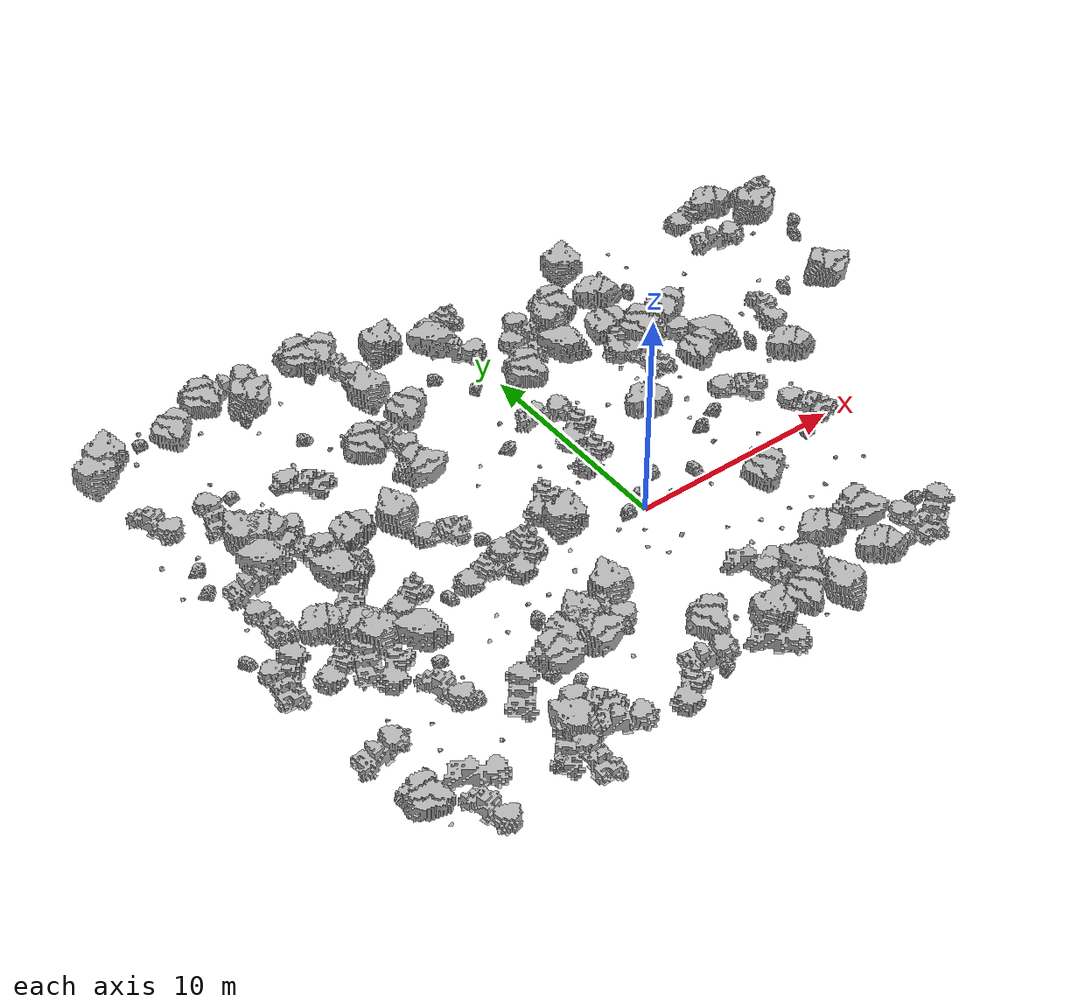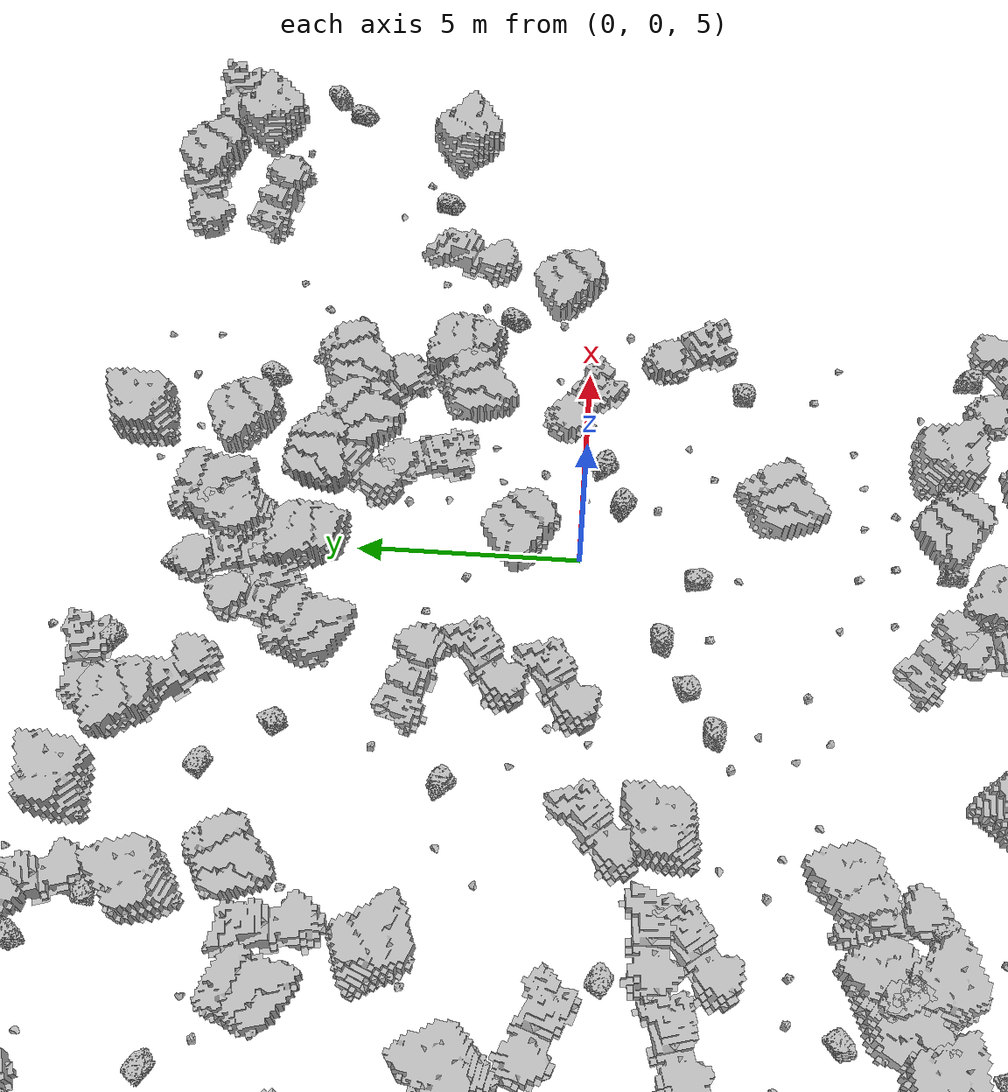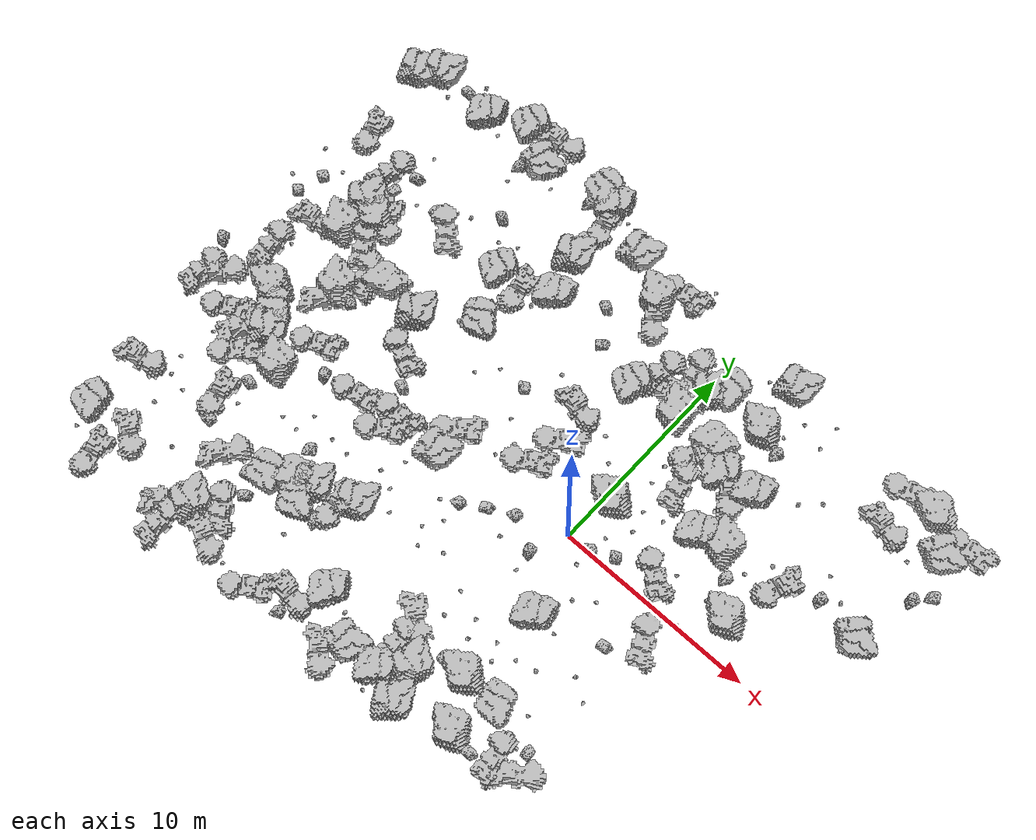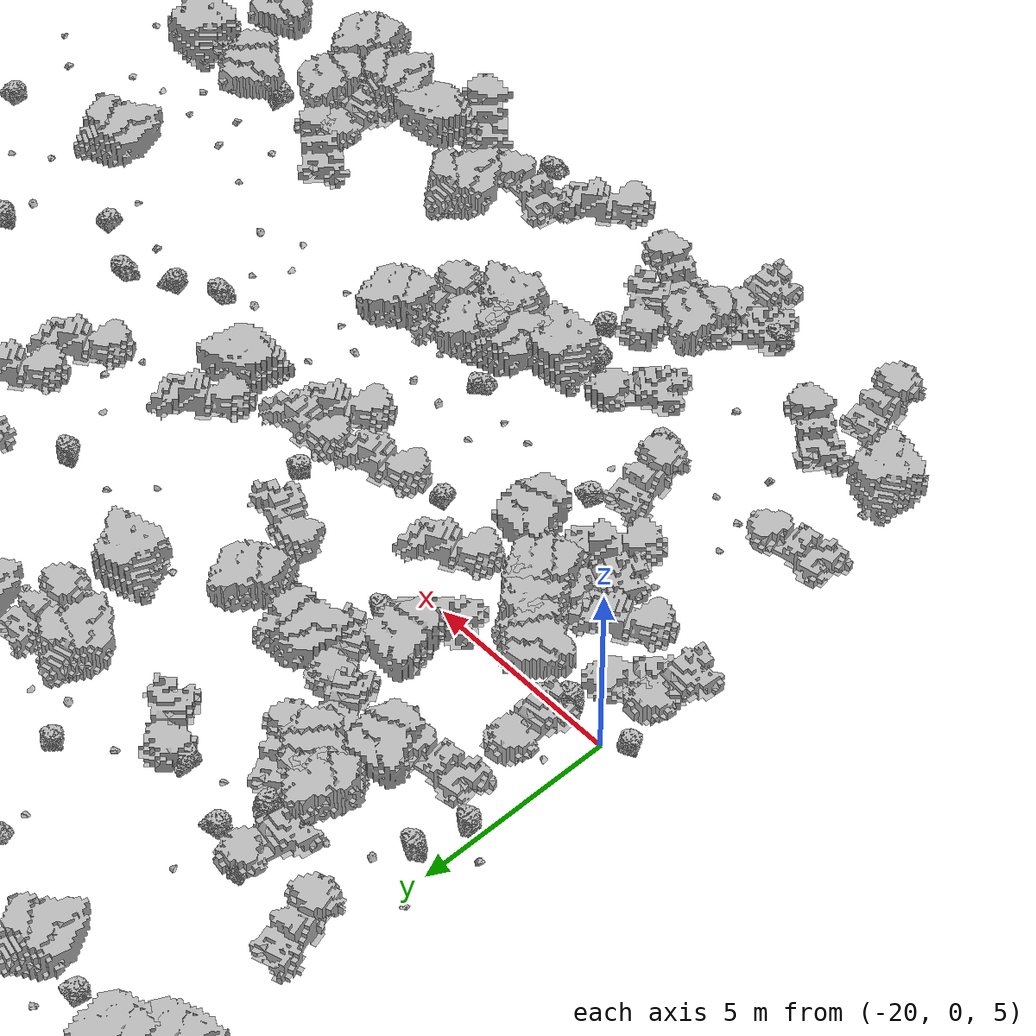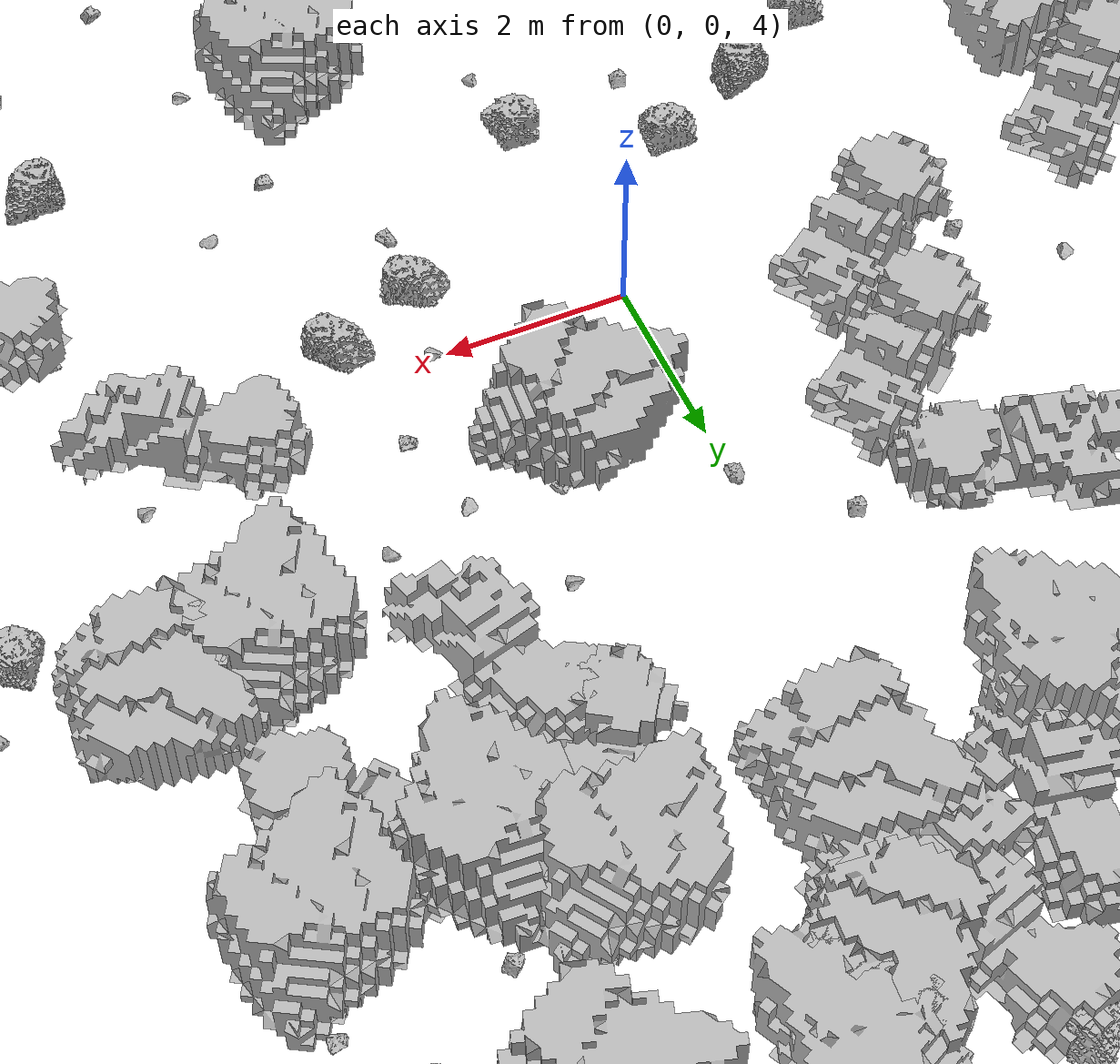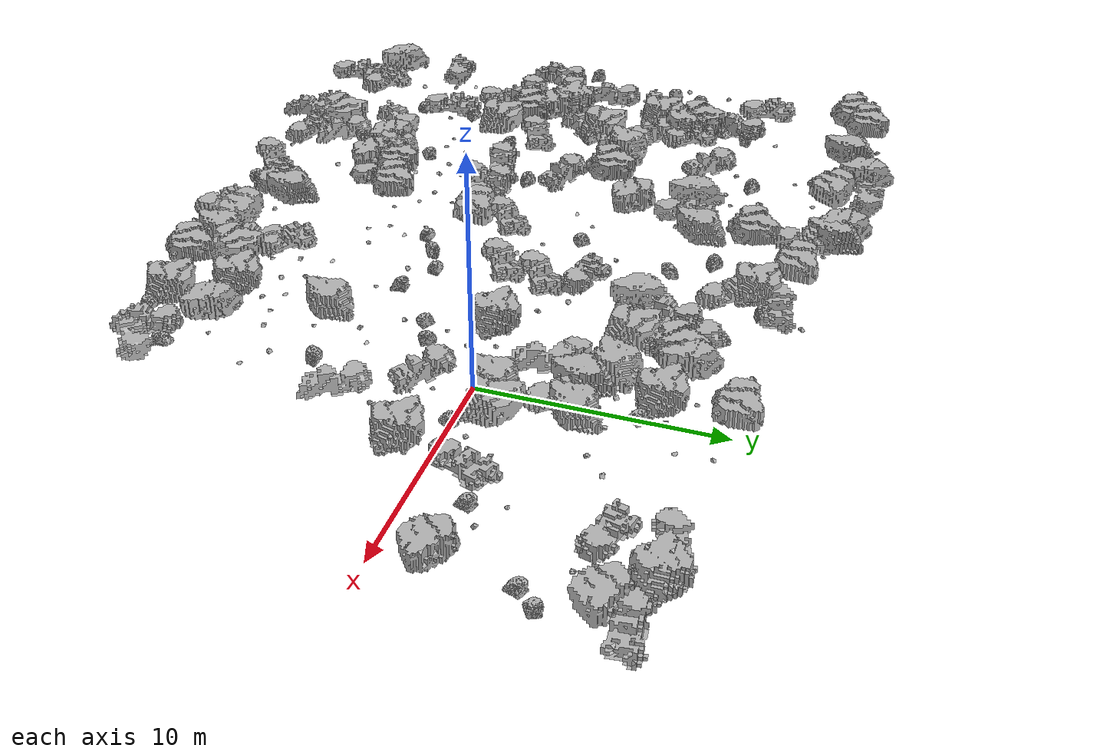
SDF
<sdf version="1.7">
 <world name="marsyard">
  <gravity>0 0 -9.81</gravity>
  <physics name="dart_physics" type="ignored">
   <max_step_size>0.003</max_step_size>
   <real_time_update_rate>333</real_time_update_rate>
   <real_time_factor>1.0</real_time_factor>
  </physics>
  <plugin filename="ignition-gazebo-physics-system" name="ignition::gazebo::systems::Physics"/>
  <plugin filename="ignition-gazebo-user-commands-system" name="ignition::gazebo::systems::UserCommands"/>
  <plugin filename="ignition-gazebo-scene-broadcaster-system" name="ignition::gazebo::systems::SceneBroadcaster"/>
  <plugin filename="ignition-gazebo-contact-system" name="ignition::gazebo::systems::Contact"/>
  <scene>
   <ambient>0.95 0.95 0.95 1</ambient>
   <background>0.70 0.70 0.70 1</background>
   <shadows>false</shadows>
  </scene>
  <light type="directional" name="sun">
   <cast_shadows>false</cast_shadows>
   <pose>0 0 30 0 0 0</pose>
   <diffuse>1 1 1 1</diffuse>
   <specular>0.15 0.15 0.15 1</specular>
   <direction>-0.35 0.1 -0.93</direction>
  </light>
  <model name="Rock_2">
   <static>true</static>
   <pose>-15.3373 -2.6823 4.0000 0.0000 0.0000 -0.1930</pose>
   <link name="link">
    <visual name="visual">
     <geometry><mesh><uri>package://rock_generator/rocks_ws/rock_1/meshes/rock_1.stl</uri></mesh></geometry>
    </visual>
    <collision name="collision">
     <geometry><mesh><uri>package://rock_generator/rocks_ws/rock_1/meshes/rock_1.stl</uri></mesh></geometry>
    </collision>
   </link>
  </model>
  <model name="Rock_3">
   <static>true</static>
   <pose>-12.5866 2.8986 4.0000 0.0000 0.0000 1.7044</pose>
   <link name="link">
    <visual name="visual">
     <geometry><mesh><uri>package://rock_generator/rocks_ws/rock_9/meshes/rock_9.stl</uri></mesh></geometry>
    </visual>
    <collision name="collision">
     <geometry><mesh><uri>package://rock_generator/rocks_ws/rock_9/meshes/rock_9.stl</uri></mesh></geometry>
    </collision>
   </link>
  </model>
  <model name="Rock_6">
   <static>true</static>
   <pose>-16.6713 -2.3727 4.0000 0.0000 0.0000 2.2812</pose>
   <link name="link">
    <visual name="visual">
     <geometry><mesh><uri>package://rock_generator/rocks_ws/rock_9/meshes/rock_9.stl</uri></mesh></geometry>
    </visual>
    <collision name="collision">
     <geometry><mesh><uri>package://rock_generator/rocks_ws/rock_9/meshes/rock_9.stl</uri></mesh></geometry>
    </collision>
   </link>
  </model>
  <model name="Rock_12">
   <static>true</static>
   <pose>-0.6498 -7.1682 4.0000 0.0000 0.0000 -2.5445</pose>
   <link name="link">
    <visual name="visual">
     <geometry><mesh><uri>package://rock_generator/rocks_ws/rock_9/meshes/rock_9.stl</uri></mesh></geometry>
    </visual>
    <collision name="collision">
     <geometry><mesh><uri>package://rock_generator/rocks_ws/rock_9/meshes/rock_9.stl</uri></mesh></geometry>
    </collision>
   </link>
  </model>
  <model name="Rock_13">
   <static>true</static>
   <pose>-10.3107 -2.4122 4.0000 0.0000 0.0000 0.2641</pose>
   <link name="link">
    <visual name="visual">
     <geometry><mesh><uri>package://rock_generator/rocks_ws/rock_2/meshes/rock_2.stl</uri></mesh></geometry>
    </visual>
    <collision name="collision">
     <geometry><mesh><uri>package://rock_generator/rocks_ws/rock_2/meshes/rock_2.stl</uri></mesh></geometry>
    </collision>
   </link>
  </model>
  <model name="Rock_15">
   <static>true</static>
   <pose>-3.9417 -0.4002 4.0000 0.0000 0.0000 -1.1793</pose>
   <link name="link">
    <visual name="visual">
     <geometry><mesh><uri>package://rock_generator/rocks_ws/rock_7/meshes/rock_7.stl</uri></mesh></geometry>
    </visual>
    <collision name="collision">
     <geometry><mesh><uri>package://rock_generator/rocks_ws/rock_7/meshes/rock_7.stl</uri></mesh></geometry>
    </collision>
   </link>
  </model>
  <model name="Rock_16">
   <static>true</static>
   <pose>-9.6234 6.0666 4.0000 0.0000 0.0000 -2.8891</pose>
   <link name="link">
    <visual name="visual">
     <geometry><mesh><uri>package://rock_generator/rocks_ws/rock_1/meshes/rock_1.stl</uri></mesh></geometry>
    </visual>
    <collision name="collision">
     <geometry><mesh><uri>package://rock_generator/rocks_ws/rock_1/meshes/rock_1.stl</uri></mesh></geometry>
    </collision>
   </link>
  </model>
  <model name="Rock_23">
   <static>true</static>
   <pose>-12.9119 -11.3638 4.0000 0.0000 0.0000 -2.2893</pose>
   <link name="link">
    <visual name="visual">
     <geometry><mesh><uri>package://rock_generator/rocks_ws/rock_2/meshes/rock_2.stl</uri></mesh></geometry>
    </visual>
    <collision name="collision">
     <geometry><mesh><uri>package://rock_generator/rocks_ws/rock_2/meshes/rock_2.stl</uri></mesh></geometry>
    </collision>
   </link>
  </model>
  <model name="Rock_24">
   <static>true</static>
   <pose>-1.0748 -10.8772 4.0000 0.0000 0.0000 2.8765</pose>
   <link name="link">
    <visual name="visual">
     <geometry><mesh><uri>package://rock_generator/rocks_ws/rock_1/meshes/rock_1.stl</uri></mesh></geometry>
    </visual>
    <collision name="collision">
     <geometry><mesh><uri>package://rock_generator/rocks_ws/rock_1/meshes/rock_1.stl</uri></mesh></geometry>
    </collision>
   </link>
  </model>
  <model name="Rock_25">
   <static>true</static>
   <pose>-11.9536 -5.3025 4.0000 0.0000 0.0000 -2.9513</pose>
   <link name="link">
    <visual name="visual">
     <geometry><mesh><uri>package://rock_generator/rocks_ws/rock_7/meshes/rock_7.stl</uri></mesh></geometry>
    </visual>
    <collision name="collision">
     <geometry><mesh><uri>package://rock_generator/rocks_ws/rock_7/meshes/rock_7.stl</uri></mesh></geometry>
    </collision>
   </link>
  </model>
  <model name="Rock_26">
   <static>true</static>
   <pose>4.8005 8.5390 4.0000 0.0000 0.0000 2.1008</pose>
   <link name="link">
    <visual name="visual">
     <geometry><mesh><uri>package://rock_generator/rocks_ws/rock_7/meshes/rock_7.stl</uri></mesh></geometry>
    </visual>
    <collision name="collision">
     <geometry><mesh><uri>package://rock_generator/rocks_ws/rock_7/meshes/rock_7.stl</uri></mesh></geometry>
    </collision>
   </link>
  </model>
  <model name="Rock_28">
   <static>true</static>
   <pose>3.3293 -4.6848 4.0000 0.0000 0.0000 2.4654</pose>
   <link name="link">
    <visual name="visual">
     <geometry><mesh><uri>package://rock_generator/rocks_ws/rock_7/meshes/rock_7.stl</uri></mesh></geometry>
    </visual>
    <collision name="collision">
     <geometry><mesh><uri>package://rock_generator/rocks_ws/rock_7/meshes/rock_7.stl</uri></mesh></geometry>
    </collision>
   </link>
  </model>
  <model name="Rock_30">
   <static>true</static>
   <pose>-19.1105 3.0353 4.0000 0.0000 0.0000 0.2926</pose>
   <link name="link">
    <visual name="visual">
     <geometry><mesh><uri>package://rock_generator/rocks_ws/rock_3/meshes/rock_3.stl</uri></mesh></geometry>
    </visual>
    <collision name="collision">
     <geometry><mesh><uri>package://rock_generator/rocks_ws/rock_3/meshes/rock_3.stl</uri></mesh></geometry>
    </collision>
   </link>
  </model>
  <model name="Rock_32">
   <static>true</static>
   <pose>0.1189 -2.7470 4.0000 0.0000 0.0000 2.7224</pose>
   <link name="link">
    <visual name="visual">
     <geometry><mesh><uri>package://rock_generator/rocks_ws/rock_3/meshes/rock_3.stl</uri></mesh></geometry>
    </visual>
    <collision name="collision">
     <geometry><mesh><uri>package://rock_generator/rocks_ws/rock_3/meshes/rock_3.stl</uri></mesh></geometry>
    </collision>
   </link>
  </model>
  <model name="Rock_33">
   <static>true</static>
   <pose>3.6703 8.1037 4.0000 0.0000 0.0000 1.2717</pose>
   <link name="link">
    <visual name="visual">
     <geometry><mesh><uri>package://rock_generator/rocks_ws/rock_1/meshes/rock_1.stl</uri></mesh></geometry>
    </visual>
    <collision name="collision">
     <geometry><mesh><uri>package://rock_generator/rocks_ws/rock_1/meshes/rock_1.stl</uri></mesh></geometry>
    </collision>
   </link>
  </model>
  <model name="Rock_36">
   <static>true</static>
   <pose>-14.2222 -7.5461 4.0000 0.0000 0.0000 0.9857</pose>
   <link name="link">
    <visual name="visual">
     <geometry><mesh><uri>package://rock_generator/rocks_ws/rock_3/meshes/rock_3.stl</uri></mesh></geometry>
    </visual>
    <collision name="collision">
     <geometry><mesh><uri>package://rock_generator/rocks_ws/rock_3/meshes/rock_3.stl</uri></mesh></geometry>
    </collision>
   </link>
  </model>
  <model name="Rock_37">
   <static>true</static>
   <pose>13.3336 8.9582 4.0000 0.0000 0.0000 -1.4593</pose>
   <link name="link">
    <visual name="visual">
     <geometry><mesh><uri>package://rock_generator/rocks_ws/rock_1/meshes/rock_1.stl</uri></mesh></geometry>
    </visual>
    <collision name="collision">
     <geometry><mesh><uri>package://rock_generator/rocks_ws/rock_1/meshes/rock_1.stl</uri></mesh></geometry>
    </collision>
   </link>
  </model>
  <model name="Rock_38">
   <static>true</static>
   <pose>2.5234 1.8988 4.0000 0.0000 0.0000 0.5487</pose>
   <link name="link">
    <visual name="visual">
     <geometry><mesh><uri>package://rock_generator/rocks_ws/rock_7/meshes/rock_7.stl</uri></mesh></geometry>
    </visual>
    <collision name="collision">
     <geometry><mesh><uri>package://rock_generator/rocks_ws/rock_7/meshes/rock_7.stl</uri></mesh></geometry>
    </collision>
   </link>
  </model>
  <model name="Rock_39">
   <static>true</static>
   <pose>-5.8300 -1.8492 4.0000 0.0000 0.0000 -0.8173</pose>
   <link name="link">
    <visual name="visual">
     <geometry><mesh><uri>package://rock_generator/rocks_ws/rock_1/meshes/rock_1.stl</uri></mesh></geometry>
    </visual>
    <collision name="collision">
     <geometry><mesh><uri>package://rock_generator/rocks_ws/rock_1/meshes/rock_1.stl</uri></mesh></geometry>
    </collision>
   </link>
  </model>
  <model name="Rock_41">
   <static>true</static>
   <pose>1.0080 1.3061 4.0000 0.0000 0.0000 1.4917</pose>
   <link name="link">
    <visual name="visual">
     <geometry><mesh><uri>package://rock_generator/rocks_ws/rock_1/meshes/rock_1.stl</uri></mesh></geometry>
    </visual>
    <collision name="collision">
     <geometry><mesh><uri>package://rock_generator/rocks_ws/rock_1/meshes/rock_1.stl</uri></mesh></geometry>
    </collision>
   </link>
  </model>
  <model name="Rock_44">
   <static>true</static>
   <pose>-18.3952 -7.5008 4.0000 0.0000 0.0000 -2.9468</pose>
   <link name="link">
    <visual name="visual">
     <geometry><mesh><uri>package://rock_generator/rocks_ws/rock_2/meshes/rock_2.stl</uri></mesh></geometry>
    </visual>
    <collision name="collision">
     <geometry><mesh><uri>package://rock_generator/rocks_ws/rock_2/meshes/rock_2.stl</uri></mesh></geometry>
    </collision>
   </link>
  </model>
  <model name="Rock_46">
   <static>true</static>
   <pose>-1.1141 7.2669 4.0000 0.0000 0.0000 -1.7584</pose>
   <link name="link">
    <visual name="visual">
     <geometry><mesh><uri>package://rock_generator/rocks_ws/rock_2/meshes/rock_2.stl</uri></mesh></geometry>
    </visual>
    <collision name="collision">
     <geometry><mesh><uri>package://rock_generator/rocks_ws/rock_2/meshes/rock_2.stl</uri></mesh></geometry>
    </collision>
   </link>
  </model>
  <model name="Rock_47">
   <static>true</static>
   <pose>-4.0417 -4.9278 4.0000 0.0000 0.0000 1.3523</pose>
   <link name="link">
    <visual name="visual">
     <geometry><mesh><uri>package://rock_generator/rocks_ws/rock_7/meshes/rock_7.stl</uri></mesh></geometry>
    </visual>
    <collision name="collision">
     <geometry><mesh><uri>package://rock_generator/rocks_ws/rock_7/meshes/rock_7.stl</uri></mesh></geometry>
    </collision>
   </link>
  </model>
  <model name="Rock_50">
   <static>true</static>
   <pose>-16.2427 -10.4047 4.0000 0.0000 0.0000 2.5466</pose>
   <link name="link">
    <visual name="visual">
     <geometry><mesh><uri>package://rock_generator/rocks_ws/rock_2/meshes/rock_2.stl</uri></mesh></geometry>
    </visual>
    <collision name="collision">
     <geometry><mesh><uri>package://rock_generator/rocks_ws/rock_2/meshes/rock_2.stl</uri></mesh></geometry>
    </collision>
   </link>
  </model>
  <model name="Rock_53">
   <static>true</static>
   <pose>0.2529 -3.6524 4.0000 0.0000 0.0000 -2.4462</pose>
   <link name="link">
    <visual name="visual">
     <geometry><mesh><uri>package://rock_generator/rocks_ws/rock_7/meshes/rock_7.stl</uri></mesh></geometry>
    </visual>
    <collision name="collision">
     <geometry><mesh><uri>package://rock_generator/rocks_ws/rock_7/meshes/rock_7.stl</uri></mesh></geometry>
    </collision>
   </link>
  </model>
  <model name="Rock_55">
   <static>true</static>
   <pose>-14.0027 -3.7306 4.0000 0.0000 0.0000 0.8740</pose>
   <link name="link">
    <visual name="visual">
     <geometry><mesh><uri>package://rock_generator/rocks_ws/rock_1/meshes/rock_1.stl</uri></mesh></geometry>
    </visual>
    <collision name="collision">
     <geometry><mesh><uri>package://rock_generator/rocks_ws/rock_1/meshes/rock_1.stl</uri></mesh></geometry>
    </collision>
   </link>
  </model>
  <model name="Rock_56">
   <static>true</static>
   <pose>-2.6793 0.2716 4.0000 0.0000 0.0000 0.6195</pose>
   <link name="link">
    <visual name="visual">
     <geometry><mesh><uri>package://rock_generator/rocks_ws/rock_2/meshes/rock_2.stl</uri></mesh></geometry>
    </visual>
    <collision name="collision">
     <geometry><mesh><uri>package://rock_generator/rocks_ws/rock_2/meshes/rock_2.stl</uri></mesh></geometry>
    </collision>
   </link>
  </model>
  <model name="Rock_58">
   <static>true</static>
   <pose>5.2382 -5.4656 4.0000 0.0000 0.0000 -1.2231</pose>
   <link name="link">
    <visual name="visual">
     <geometry><mesh><uri>package://rock_generator/rocks_ws/rock_9/meshes/rock_9.stl</uri></mesh></geometry>
    </visual>
    <collision name="collision">
     <geometry><mesh><uri>package://rock_generator/rocks_ws/rock_9/meshes/rock_9.stl</uri></mesh></geometry>
    </collision>
   </link>
  </model>
  <model name="Rock_60">
   <static>true</static>
   <pose>-9.3885 3.1634 4.0000 0.0000 0.0000 -2.7937</pose>
   <link name="link">
    <visual name="visual">
     <geometry><mesh><uri>package://rock_generator/rocks_ws/rock_9/meshes/rock_9.stl</uri></mesh></geometry>
    </visual>
    <collision name="collision">
     <geometry><mesh><uri>package://rock_generator/rocks_ws/rock_9/meshes/rock_9.stl</uri></mesh></geometry>
    </collision>
   </link>
  </model>
  <model name="Rock_61">
   <static>true</static>
   <pose>-6.8671 -5.8648 4.0000 0.0000 0.0000 -0.4022</pose>
   <link name="link">
    <visual name="visual">
     <geometry><mesh><uri>package://rock_generator/rocks_ws/rock_1/meshes/rock_1.stl</uri></mesh></geometry>
    </visual>
    <collision name="collision">
     <geometry><mesh><uri>package://rock_generator/rocks_ws/rock_1/meshes/rock_1.stl</uri></mesh></geometry>
    </collision>
   </link>
  </model>
  <model name="Rock_62">
   <static>true</static>
   <pose>-1.3756 -8.1738 4.0000 0.0000 0.0000 2.4767</pose>
   <link name="link">
    <visual name="visual">
     <geometry><mesh><uri>package://rock_generator/rocks_ws/rock_2/meshes/rock_2.stl</uri></mesh></geometry>
    </visual>
    <collision name="collision">
     <geometry><mesh><uri>package://rock_generator/rocks_ws/rock_2/meshes/rock_2.stl</uri></mesh></geometry>
    </collision>
   </link>
  </model>
  <model name="Rock_63">
   <static>true</static>
   <pose>-5.9303 -0.6999 4.0000 0.0000 0.0000 0.7273</pose>
   <link name="link">
    <visual name="visual">
     <geometry><mesh><uri>package://rock_generator/rocks_ws/rock_2/meshes/rock_2.stl</uri></mesh></geometry>
    </visual>
    <collision name="collision">
     <geometry><mesh><uri>package://rock_generator/rocks_ws/rock_2/meshes/rock_2.stl</uri></mesh></geometry>
    </collision>
   </link>
  </model>
  <model name="Rock_64">
   <static>true</static>
   <pose>-1.4319 -1.8924 4.0000 0.0000 0.0000 0.9817</pose>
   <link name="link">
    <visual name="visual">
     <geometry><mesh><uri>package://rock_generator/rocks_ws/rock_3/meshes/rock_3.stl</uri></mesh></geometry>
    </visual>
    <collision name="collision">
     <geometry><mesh><uri>package://rock_generator/rocks_ws/rock_3/meshes/rock_3.stl</uri></mesh></geometry>
    </collision>
   </link>
  </model>
  <model name="Rock_69">
   <static>true</static>
   <pose>-8.5305 3.8011 4.0000 0.0000 0.0000 -1.9772</pose>
   <link name="link">
    <visual name="visual">
     <geometry><mesh><uri>package://rock_generator/rocks_ws/rock_1/meshes/rock_1.stl</uri></mesh></geometry>
    </visual>
    <collision name="collision">
     <geometry><mesh><uri>package://rock_generator/rocks_ws/rock_1/meshes/rock_1.stl</uri></mesh></geometry>
    </collision>
   </link>
  </model>
  <model name="Rock_70">
   <static>true</static>
   <pose>-16.5224 4.8071 4.0000 0.0000 0.0000 0.0338</pose>
   <link name="link">
    <visual name="visual">
     <geometry><mesh><uri>package://rock_generator/rocks_ws/rock_1/meshes/rock_1.stl</uri></mesh></geometry>
    </visual>
    <collision name="collision">
     <geometry><mesh><uri>package://rock_generator/rocks_ws/rock_1/meshes/rock_1.stl</uri></mesh></geometry>
    </collision>
   </link>
  </model>
  <model name="Rock_71">
   <static>true</static>
   <pose>5.7069 6.7457 4.0000 0.0000 0.0000 1.7021</pose>
   <link name="link">
    <visual name="visual">
     <geometry><mesh><uri>package://rock_generator/rocks_ws/rock_9/meshes/rock_9.stl</uri></mesh></geometry>
    </visual>
    <collision name="collision">
     <geometry><mesh><uri>package://rock_generator/rocks_ws/rock_9/meshes/rock_9.stl</uri></mesh></geometry>
    </collision>
   </link>
  </model>
  <model name="Rock_72">
   <static>true</static>
   <pose>-15.6774 -4.5340 4.0000 0.0000 0.0000 0.8496</pose>
   <link name="link">
    <visual name="visual">
     <geometry><mesh><uri>package://rock_generator/rocks_ws/rock_2/meshes/rock_2.stl</uri></mesh></geometry>
    </visual>
    <collision name="collision">
     <geometry><mesh><uri>package://rock_generator/rocks_ws/rock_2/meshes/rock_2.stl</uri></mesh></geometry>
    </collision>
   </link>
  </model>
  <model name="Rock_74">
   <static>true</static>
   <pose>-8.3867 5.9427 4.0000 0.0000 0.0000 1.7308</pose>
   <link name="link">
    <visual name="visual">
     <geometry><mesh><uri>package://rock_generator/rocks_ws/rock_2/meshes/rock_2.stl</uri></mesh></geometry>
    </visual>
    <collision name="collision">
     <geometry><mesh><uri>package://rock_generator/rocks_ws/rock_2/meshes/rock_2.stl</uri></mesh></geometry>
    </collision>
   </link>
  </model>
  <model name="Rock_75">
   <static>true</static>
   <pose>4.0380 6.6683 4.0000 0.0000 0.0000 -1.9028</pose>
   <link name="link">
    <visual name="visual">
     <geometry><mesh><uri>package://rock_generator/rocks_ws/rock_9/meshes/rock_9.stl</uri></mesh></geometry>
    </visual>
    <collision name="collision">
     <geometry><mesh><uri>package://rock_generator/rocks_ws/rock_9/meshes/rock_9.stl</uri></mesh></geometry>
    </collision>
   </link>
  </model>
  <model name="Rock_76">
   <static>true</static>
   <pose>-11.9440 -2.7662 4.0000 0.0000 0.0000 2.8580</pose>
   <link name="link">
    <visual name="visual">
     <geometry><mesh><uri>package://rock_generator/rocks_ws/rock_3/meshes/rock_3.stl</uri></mesh></geometry>
    </visual>
    <collision name="collision">
     <geometry><mesh><uri>package://rock_generator/rocks_ws/rock_3/meshes/rock_3.stl</uri></mesh></geometry>
    </collision>
   </link>
  </model>
  <model name="Rock_77">
   <static>true</static>
   <pose>-18.1683 -0.8440 4.0000 0.0000 0.0000 0.3233</pose>
   <link name="link">
    <visual name="visual">
     <geometry><mesh><uri>package://rock_generator/rocks_ws/rock_3/meshes/rock_3.stl</uri></mesh></geometry>
    </visual>
    <collision name="collision">
     <geometry><mesh><uri>package://rock_generator/rocks_ws/rock_3/meshes/rock_3.stl</uri></mesh></geometry>
    </collision>
   </link>
  </model>
  <model name="Rock_80">
   <static>true</static>
   <pose>5.9154 3.0739 4.0000 0.0000 0.0000 0.6500</pose>
   <link name="link">
    <visual name="visual">
     <geometry><mesh><uri>package://rock_generator/rocks_ws/rock_1/meshes/rock_1.stl</uri></mesh></geometry>
    </visual>
    <collision name="collision">
     <geometry><mesh><uri>package://rock_generator/rocks_ws/rock_1/meshes/rock_1.stl</uri></mesh></geometry>
    </collision>
   </link>
  </model>
  <model name="Rock_82">
   <static>true</static>
   <pose>3.7152 -2.4698 4.0000 0.0000 0.0000 -0.4432</pose>
   <link name="link">
    <visual name="visual">
     <geometry><mesh><uri>package://rock_generator/rocks_ws/rock_7/meshes/rock_7.stl</uri></mesh></geometry>
    </visual>
    <collision name="collision">
     <geometry><mesh><uri>package://rock_generator/rocks_ws/rock_7/meshes/rock_7.stl</uri></mesh></geometry>
    </collision>
   </link>
  </model>
  <model name="Rock_84">
   <static>true</static>
   <pose>-1.2791 -3.0156 4.0000 0.0000 0.0000 -1.1472</pose>
   <link name="link">
    <visual name="visual">
     <geometry><mesh><uri>package://rock_generator/rocks_ws/rock_9/meshes/rock_9.stl</uri></mesh></geometry>
    </visual>
    <collision name="collision">
     <geometry><mesh><uri>package://rock_generator/rocks_ws/rock_9/meshes/rock_9.stl</uri></mesh></geometry>
    </collision>
   </link>
  </model>
  <model name="Rock_86">
   <static>true</static>
   <pose>-8.7033 -4.6993 4.0000 0.0000 0.0000 -0.2556</pose>
   <link name="link">
    <visual name="visual">
     <geometry><mesh><uri>package://rock_generator/rocks_ws/rock_9/meshes/rock_9.stl</uri></mesh></geometry>
    </visual>
    <collision name="collision">
     <geometry><mesh><uri>package://rock_generator/rocks_ws/rock_9/meshes/rock_9.stl</uri></mesh></geometry>
    </collision>
   </link>
  </model>
  <model name="Rock_87">
   <static>true</static>
   <pose>-11.7268 11.4727 4.0000 0.0000 0.0000 -1.3000</pose>
   <link name="link">
    <visual name="visual">
     <geometry><mesh><uri>package://rock_generator/rocks_ws/rock_1/meshes/rock_1.stl</uri></mesh></geometry>
    </visual>
    <collision name="collision">
     <geometry><mesh><uri>package://rock_generator/rocks_ws/rock_1/meshes/rock_1.stl</uri></mesh></geometry>
    </collision>
   </link>
  </model>
  <model name="Rock_90">
   <static>true</static>
   <pose>4.6733 5.8507 4.0000 0.0000 0.0000 3.1198</pose>
   <link name="link">
    <visual name="visual">
     <geometry><mesh><uri>package://rock_generator/rocks_ws/rock_9/meshes/rock_9.stl</uri></mesh></geometry>
    </visual>
    <collision name="collision">
     <geometry><mesh><uri>package://rock_generator/rocks_ws/rock_9/meshes/rock_9.stl</uri></mesh></geometry>
    </collision>
   </link>
  </model>
  <model name="Rock_91">
   <static>true</static>
   <pose>3.0340 -0.4156 4.0000 0.0000 0.0000 0.0920</pose>
   <link name="link">
    <visual name="visual">
     <geometry><mesh><uri>package://rock_generator/rocks_ws/rock_3/meshes/rock_3.stl</uri></mesh></geometry>
    </visual>
    <collision name="collision">
     <geometry><mesh><uri>package://rock_generator/rocks_ws/rock_3/meshes/rock_3.stl</uri></mesh></geometry>
    </collision>
   </link>
  </model>
  <model name="Rock_92">
   <static>true</static>
   <pose>0.4650 -6.4125 4.0000 0.0000 0.0000 -0.8018</pose>
   <link name="link">
    <visual name="visual">
     <geometry><mesh><uri>package://rock_generator/rocks_ws/rock_9/meshes/rock_9.stl</uri></mesh></geometry>
    </visual>
    <collision name="collision">
     <geometry><mesh><uri>package://rock_generator/rocks_ws/rock_9/meshes/rock_9.stl</uri></mesh></geometry>
    </collision>
   </link>
  </model>
  <model name="Rock_93">
   <static>true</static>
   <pose>0.7902 -7.2652 4.0000 0.0000 0.0000 -1.0564</pose>
   <link name="link">
    <visual name="visual">
     <geometry><mesh><uri>package://rock_generator/rocks_ws/rock_9/meshes/rock_9.stl</uri></mesh></geometry>
    </visual>
    <collision name="collision">
     <geometry><mesh><uri>package://rock_generator/rocks_ws/rock_9/meshes/rock_9.stl</uri></mesh></geometry>
    </collision>
   </link>
  </model>
  <model name="Rock_95">
   <static>true</static>
   <pose>-5.9957 -10.9134 4.0000 0.0000 0.0000 3.0316</pose>
   <link name="link">
    <visual name="visual">
     <geometry><mesh><uri>package://rock_generator/rocks_ws/rock_2/meshes/rock_2.stl</uri></mesh></geometry>
    </visual>
    <collision name="collision">
     <geometry><mesh><uri>package://rock_generator/rocks_ws/rock_2/meshes/rock_2.stl</uri></mesh></geometry>
    </collision>
   </link>
  </model>
  <model name="Rock_97">
   <static>true</static>
   <pose>-17.3370 5.5142 4.0000 0.0000 0.0000 1.4713</pose>
   <link name="link">
    <visual name="visual">
     <geometry><mesh><uri>package://rock_generator/rocks_ws/rock_9/meshes/rock_9.stl</uri></mesh></geometry>
    </visual>
    <collision name="collision">
     <geometry><mesh><uri>package://rock_generator/rocks_ws/rock_9/meshes/rock_9.stl</uri></mesh></geometry>
    </collision>
   </link>
  </model>
  <model name="Rock_100">
   <static>true</static>
   <pose>-7.6845 10.8635 4.0000 0.0000 0.0000 1.8561</pose>
   <link name="link">
    <visual name="visual">
     <geometry><mesh><uri>package://rock_generator/rocks_ws/rock_2/meshes/rock_2.stl</uri></mesh></geometry>
    </visual>
    <collision name="collision">
     <geometry><mesh><uri>package://rock_generator/rocks_ws/rock_2/meshes/rock_2.stl</uri></mesh></geometry>
    </collision>
   </link>
  </model>
  <model name="Rock_103">
   <static>true</static>
   <pose>-4.3196 -3.5071 4.0000 0.0000 0.0000 0.8779</pose>
   <link name="link">
    <visual name="visual">
     <geometry><mesh><uri>package://rock_generator/rocks_ws/rock_9/meshes/rock_9.stl</uri></mesh></geometry>
    </visual>
    <collision name="collision">
     <geometry><mesh><uri>package://rock_generator/rocks_ws/rock_9/meshes/rock_9.stl</uri></mesh></geometry>
    </collision>
   </link>
  </model>
  <model name="Rock_104">
   <static>true</static>
   <pose>-7.2279 1.8346 4.0000 0.0000 0.0000 -0.4660</pose>
   <link name="link">
    <visual name="visual">
     <geometry><mesh><uri>package://rock_generator/rocks_ws/rock_7/meshes/rock_7.stl</uri></mesh></geometry>
    </visual>
    <collision name="collision">
     <geometry><mesh><uri>package://rock_generator/rocks_ws/rock_7/meshes/rock_7.stl</uri></mesh></geometry>
    </collision>
   </link>
  </model>
  <model name="Rock_105">
   <static>true</static>
   <pose>5.4657 0.7225 4.0000 0.0000 0.0000 -3.0356</pose>
   <link name="link">
    <visual name="visual">
     <geometry><mesh><uri>package://rock_generator/rocks_ws/rock_7/meshes/rock_7.stl</uri></mesh></geometry>
    </visual>
    <collision name="collision">
     <geometry><mesh><uri>package://rock_generator/rocks_ws/rock_7/meshes/rock_7.stl</uri></mesh></geometry>
    </collision>
   </link>
  </model>
  <model name="Rock_106">
   <static>true</static>
   <pose>-2.5404 -5.1986 4.0000 0.0000 0.0000 0.9231</pose>
   <link name="link">
    <visual name="visual">
     <geometry><mesh><uri>package://rock_generator/rocks_ws/rock_9/meshes/rock_9.stl</uri></mesh></geometry>
    </visual>
    <collision name="collision">
     <geometry><mesh><uri>package://rock_generator/rocks_ws/rock_9/meshes/rock_9.stl</uri></mesh></geometry>
    </collision>
   </link>
  </model>
  <model name="Rock_110">
   <static>true</static>
   <pose>-13.2644 -1.8583 4.0000 0.0000 0.0000 0.4791</pose>
   <link name="link">
    <visual name="visual">
     <geometry><mesh><uri>package://rock_generator/rocks_ws/rock_2/meshes/rock_2.stl</uri></mesh></geometry>
    </visual>
    <collision name="collision">
     <geometry><mesh><uri>package://rock_generator/rocks_ws/rock_2/meshes/rock_2.stl</uri></mesh></geometry>
    </collision>
   </link>
  </model>
  <model name="Rock_113">
   <static>true</static>
   <pose>-7.3317 -2.1131 4.0000 0.0000 0.0000 -2.0577</pose>
   <link name="link">
    <visual name="visual">
     <geometry><mesh><uri>package://rock_generator/rocks_ws/rock_7/meshes/rock_7.stl</uri></mesh></geometry>
    </visual>
    <collision name="collision">
     <geometry><mesh><uri>package://rock_generator/rocks_ws/rock_7/meshes/rock_7.stl</uri></mesh></geometry>
    </collision>
   </link>
  </model>
  <model name="Rock_114">
   <static>true</static>
   <pose>6.2851 9.2212 4.0000 0.0000 0.0000 -1.5591</pose>
   <link name="link">
    <visual name="visual">
     <geometry><mesh><uri>package://rock_generator/rocks_ws/rock_7/meshes/rock_7.stl</uri></mesh></geometry>
    </visual>
    <collision name="collision">
     <geometry><mesh><uri>package://rock_generator/rocks_ws/rock_7/meshes/rock_7.stl</uri></mesh></geometry>
    </collision>
   </link>
  </model>
  <model name="Rock_119">
   <static>true</static>
   <pose>2.9331 3.7971 4.0000 0.0000 0.0000 -1.2923</pose>
   <link name="link">
    <visual name="visual">
     <geometry><mesh><uri>package://rock_generator/rocks_ws/rock_2/meshes/rock_2.stl</uri></mesh></geometry>
    </visual>
    <collision name="collision">
     <geometry><mesh><uri>package://rock_generator/rocks_ws/rock_2/meshes/rock_2.stl</uri></mesh></geometry>
    </collision>
   </link>
  </model>
  <model name="Rock_123">
   <static>true</static>
   <pose>7.9945 7.3528 4.0000 0.0000 0.0000 -2.2811</pose>
   <link name="link">
    <visual name="visual">
     <geometry><mesh><uri>package://rock_generator/rocks_ws/rock_9/meshes/rock_9.stl</uri></mesh></geometry>
    </visual>
    <collision name="collision">
     <geometry><mesh><uri>package://rock_generator/rocks_ws/rock_9/meshes/rock_9.stl</uri></mesh></geometry>
    </collision>
   </link>
  </model>
  <model name="Rock_124">
   <static>true</static>
   <pose>-16.5970 -8.5785 4.0000 0.0000 0.0000 -1.3797</pose>
   <link name="link">
    <visual name="visual">
     <geometry><mesh><uri>package://rock_generator/rocks_ws/rock_9/meshes/rock_9.stl</uri></mesh></geometry>
    </visual>
    <collision name="collision">
     <geometry><mesh><uri>package://rock_generator/rocks_ws/rock_9/meshes/rock_9.stl</uri></mesh></geometry>
    </collision>
   </link>
  </model>
  <model name="Rock_125">
   <static>true</static>
   <pose>10.4033 10.1896 4.0000 0.0000 0.0000 0.2892</pose>
   <link name="link">
    <visual name="visual">
     <geometry><mesh><uri>package://rock_generator/rocks_ws/rock_2/meshes/rock_2.stl</uri></mesh></geometry>
    </visual>
    <collision name="collision">
     <geometry><mesh><uri>package://rock_generator/rocks_ws/rock_2/meshes/rock_2.stl</uri></mesh></geometry>
    </collision>
   </link>
  </model>
  <model name="Rock_126">
   <static>true</static>
   <pose>-3.8596 6.4867 4.0000 0.0000 0.0000 -1.3820</pose>
   <link name="link">
    <visual name="visual">
     <geometry><mesh><uri>package://rock_generator/rocks_ws/rock_3/meshes/rock_3.stl</uri></mesh></geometry>
    </visual>
    <collision name="collision">
     <geometry><mesh><uri>package://rock_generator/rocks_ws/rock_3/meshes/rock_3.stl</uri></mesh></geometry>
    </collision>
   </link>
  </model>
  <model name="Rock_128">
   <static>true</static>
   <pose>4.1983 0.8187 4.0000 0.0000 0.0000 -2.3443</pose>
   <link name="link">
    <visual name="visual">
     <geometry><mesh><uri>package://rock_generator/rocks_ws/rock_7/meshes/rock_7.stl</uri></mesh></geometry>
    </visual>
    <collision name="collision">
     <geometry><mesh><uri>package://rock_generator/rocks_ws/rock_7/meshes/rock_7.stl</uri></mesh></geometry>
    </collision>
   </link>
  </model>
  <model name="Rock_129">
   <static>true</static>
   <pose>6.8617 -0.9495 4.0000 0.0000 0.0000 1.0533</pose>
   <link name="link">
    <visual name="visual">
     <geometry><mesh><uri>package://rock_generator/rocks_ws/rock_9/meshes/rock_9.stl</uri></mesh></geometry>
    </visual>
    <collision name="collision">
     <geometry><mesh><uri>package://rock_generator/rocks_ws/rock_9/meshes/rock_9.stl</uri></mesh></geometry>
    </collision>
   </link>
  </model>
  <model name="Rock_130">
   <static>true</static>
   <pose>-0.1229 9.2451 4.0000 0.0000 0.0000 -1.0116</pose>
   <link name="link">
    <visual name="visual">
     <geometry><mesh><uri>package://rock_generator/rocks_ws/rock_3/meshes/rock_3.stl</uri></mesh></geometry>
    </visual>
    <collision name="collision">
     <geometry><mesh><uri>package://rock_generator/rocks_ws/rock_3/meshes/rock_3.stl</uri></mesh></geometry>
    </collision>
   </link>
  </model>
  <model name="Rock_132">
   <static>true</static>
   <pose>-15.0006 4.5964 4.0000 0.0000 0.0000 2.2051</pose>
   <link name="link">
    <visual name="visual">
     <geometry><mesh><uri>package://rock_generator/rocks_ws/rock_2/meshes/rock_2.stl</uri></mesh></geometry>
    </visual>
    <collision name="collision">
     <geometry><mesh><uri>package://rock_generator/rocks_ws/rock_2/meshes/rock_2.stl</uri></mesh></geometry>
    </collision>
   </link>
  </model>
  <model name="Rock_134">
   <static>true</static>
   <pose>-8.6392 -7.6802 4.0000 0.0000 0.0000 -1.8784</pose>
   <link name="link">
    <visual name="visual">
     <geometry><mesh><uri>package://rock_generator/rocks_ws/rock_1/meshes/rock_1.stl</uri></mesh></geometry>
    </visual>
    <collision name="collision">
     <geometry><mesh><uri>package://rock_generator/rocks_ws/rock_1/meshes/rock_1.stl</uri></mesh></geometry>
    </collision>
   </link>
  </model>
  <model name="Rock_135">
   <static>true</static>
   <pose>-17.4097 11.0608 4.0000 0.0000 0.0000 2.5920</pose>
   <link name="link">
    <visual name="visual">
     <geometry><mesh><uri>package://rock_generator/rocks_ws/rock_9/meshes/rock_9.stl</uri></mesh></geometry>
    </visual>
    <collision name="collision">
     <geometry><mesh><uri>package://rock_generator/rocks_ws/rock_9/meshes/rock_9.stl</uri></mesh></geometry>
    </collision>
   </link>
  </model>
  <model name="Rock_139">
   <static>true</static>
   <pose>-17.2862 -6.2772 4.0000 0.0000 0.0000 -0.4546</pose>
   <link name="link">
    <visual name="visual">
     <geometry><mesh><uri>package://rock_generator/rocks_ws/rock_7/meshes/rock_7.stl</uri></mesh></geometry>
    </visual>
    <collision name="collision">
     <geometry><mesh><uri>package://rock_generator/rocks_ws/rock_7/meshes/rock_7.stl</uri></mesh></geometry>
    </collision>
   </link>
  </model>
  <model name="Rock_141">
   <static>true</static>
   <pose>-18.2878 -11.6133 4.0000 0.0000 0.0000 2.7403</pose>
   <link name="link">
    <visual name="visual">
     <geometry><mesh><uri>package://rock_generator/rocks_ws/rock_7/meshes/rock_7.stl</uri></mesh></geometry>
    </visual>
    <collision name="collision">
     <geometry><mesh><uri>package://rock_generator/rocks_ws/rock_7/meshes/rock_7.stl</uri></mesh></geometry>
    </collision>
   </link>
  </model>
  <model name="Rock_143">
   <static>true</static>
   <pose>1.3108 5.9522 4.0000 0.0000 0.0000 -1.1698</pose>
   <link name="link">
    <visual name="visual">
     <geometry><mesh><uri>package://rock_generator/rocks_ws/rock_7/meshes/rock_7.stl</uri></mesh></geometry>
    </visual>
    <collision name="collision">
     <geometry><mesh><uri>package://rock_generator/rocks_ws/rock_7/meshes/rock_7.stl</uri></mesh></geometry>
    </collision>
   </link>
  </model>
  <model name="Rock_148">
   <static>true</static>
   <pose>-3.7696 9.8197 4.0000 0.0000 0.0000 1.0498</pose>
   <link name="link">
    <visual name="visual">
     <geometry><mesh><uri>package://rock_generator/rocks_ws/rock_1/meshes/rock_1.stl</uri></mesh></geometry>
    </visual>
    <collision name="collision">
     <geometry><mesh><uri>package://rock_generator/rocks_ws/rock_1/meshes/rock_1.stl</uri></mesh></geometry>
    </collision>
   </link>
  </model>
  <model name="Rock_152">
   <static>true</static>
   <pose>-16.8182 -12.1159 4.0000 0.0000 0.0000 1.7944</pose>
   <link name="link">
    <visual name="visual">
     <geometry><mesh><uri>package://rock_generator/rocks_ws/rock_2/meshes/rock_2.stl</uri></mesh></geometry>
    </visual>
    <collision name="collision">
     <geometry><mesh><uri>package://rock_generator/rocks_ws/rock_2/meshes/rock_2.stl</uri></mesh></geometry>
    </collision>
   </link>
  </model>
  <model name="Rock_153">
   <static>true</static>
   <pose>12.2811 7.7373 4.0000 0.0000 0.0000 0.3173</pose>
   <link name="link">
    <visual name="visual">
     <geometry><mesh><uri>package://rock_generator/rocks_ws/rock_9/meshes/rock_9.stl</uri></mesh></geometry>
    </visual>
    <collision name="collision">
     <geometry><mesh><uri>package://rock_generator/rocks_ws/rock_9/meshes/rock_9.stl</uri></mesh></geometry>
    </collision>
   </link>
  </model>
  <model name="Rock_159">
   <static>true</static>
   <pose>-3.0063 8.8831 4.0000 0.0000 0.0000 2.2579</pose>
   <link name="link">
    <visual name="visual">
     <geometry><mesh><uri>package://rock_generator/rocks_ws/rock_2/meshes/rock_2.stl</uri></mesh></geometry>
    </visual>
    <collision name="collision">
     <geometry><mesh><uri>package://rock_generator/rocks_ws/rock_2/meshes/rock_2.stl</uri></mesh></geometry>
    </collision>
   </link>
  </model>
  <model name="Rock_160">
   <static>true</static>
   <pose>-9.1724 -11.8180 4.0000 0.0000 0.0000 0.2420</pose>
   <link name="link">
    <visual name="visual">
     <geometry><mesh><uri>package://rock_generator/rocks_ws/rock_7/meshes/rock_7.stl</uri></mesh></geometry>
    </visual>
    <collision name="collision">
     <geometry><mesh><uri>package://rock_generator/rocks_ws/rock_7/meshes/rock_7.stl</uri></mesh></geometry>
    </collision>
   </link>
  </model>
  <model name="Rock_161">
   <static>true</static>
   <pose>-19.7115 5.3705 4.0000 0.0000 0.0000 2.2692</pose>
   <link name="link">
    <visual name="visual">
     <geometry><mesh><uri>package://rock_generator/rocks_ws/rock_9/meshes/rock_9.stl</uri></mesh></geometry>
    </visual>
    <collision name="collision">
     <geometry><mesh><uri>package://rock_generator/rocks_ws/rock_9/meshes/rock_9.stl</uri></mesh></geometry>
    </collision>
   </link>
  </model>
  <model name="Rock_162">
   <static>true</static>
   <pose>2.5464 5.2759 4.0000 0.0000 0.0000 1.0002</pose>
   <link name="link">
    <visual name="visual">
     <geometry><mesh><uri>package://rock_generator/rocks_ws/rock_2/meshes/rock_2.stl</uri></mesh></geometry>
    </visual>
    <collision name="collision">
     <geometry><mesh><uri>package://rock_generator/rocks_ws/rock_2/meshes/rock_2.stl</uri></mesh></geometry>
    </collision>
   </link>
  </model>
  <model name="Rock_163">
   <static>true</static>
   <pose>4.1939 -10.8740 4.0000 0.0000 0.0000 -2.1609</pose>
   <link name="link">
    <visual name="visual">
     <geometry><mesh><uri>package://rock_generator/rocks_ws/rock_3/meshes/rock_3.stl</uri></mesh></geometry>
    </visual>
    <collision name="collision">
     <geometry><mesh><uri>package://rock_generator/rocks_ws/rock_3/meshes/rock_3.stl</uri></mesh></geometry>
    </collision>
   </link>
  </model>
  <model name="Rock_167">
   <static>true</static>
   <pose>3.8920 5.3587 4.0000 0.0000 0.0000 3.0819</pose>
   <link name="link">
    <visual name="visual">
     <geometry><mesh><uri>package://rock_generator/rocks_ws/rock_1/meshes/rock_1.stl</uri></mesh></geometry>
    </visual>
    <collision name="collision">
     <geometry><mesh><uri>package://rock_generator/rocks_ws/rock_1/meshes/rock_1.stl</uri></mesh></geometry>
    </collision>
   </link>
  </model>
  <model name="Rock_168">
   <static>true</static>
   <pose>-18.0848 0.3081 4.0000 0.0000 0.0000 -1.4491</pose>
   <link name="link">
    <visual name="visual">
     <geometry><mesh><uri>package://rock_generator/rocks_ws/rock_2/meshes/rock_2.stl</uri></mesh></geometry>
    </visual>
    <collision name="collision">
     <geometry><mesh><uri>package://rock_generator/rocks_ws/rock_2/meshes/rock_2.stl</uri></mesh></geometry>
    </collision>
   </link>
  </model>
  <model name="Rock_169">
   <static>true</static>
   <pose>-17.3954 -3.2587 4.0000 0.0000 0.0000 0.5388</pose>
   <link name="link">
    <visual name="visual">
     <geometry><mesh><uri>package://rock_generator/rocks_ws/rock_2/meshes/rock_2.stl</uri></mesh></geometry>
    </visual>
    <collision name="collision">
     <geometry><mesh><uri>package://rock_generator/rocks_ws/rock_2/meshes/rock_2.stl</uri></mesh></geometry>
    </collision>
   </link>
  </model>
  <model name="Rock_170">
   <static>true</static>
   <pose>6.2028 -6.0811 4.0000 0.0000 0.0000 -1.7401</pose>
   <link name="link">
    <visual name="visual">
     <geometry><mesh><uri>package://rock_generator/rocks_ws/rock_7/meshes/rock_7.stl</uri></mesh></geometry>
    </visual>
    <collision name="collision">
     <geometry><mesh><uri>package://rock_generator/rocks_ws/rock_7/meshes/rock_7.stl</uri></mesh></geometry>
    </collision>
   </link>
  </model>
  <model name="Rock_173">
   <static>true</static>
   <pose>-1.6090 5.8977 4.0000 0.0000 0.0000 -2.8611</pose>
   <link name="link">
    <visual name="visual">
     <geometry><mesh><uri>package://rock_generator/rocks_ws/rock_1/meshes/rock_1.stl</uri></mesh></geometry>
    </visual>
    <collision name="collision">
     <geometry><mesh><uri>package://rock_generator/rocks_ws/rock_1/meshes/rock_1.stl</uri></mesh></geometry>
    </collision>
   </link>
  </model>
  <model name="Rock_174">
   <static>true</static>
   <pose>-15.7809 2.3304 4.0000 0.0000 0.0000 -2.2014</pose>
   <link name="link">
    <visual name="visual">
     <geometry><mesh><uri>package://rock_generator/rocks_ws/rock_7/meshes/rock_7.stl</uri></mesh></geometry>
    </visual>
    <collision name="collision">
     <geometry><mesh><uri>package://rock_generator/rocks_ws/rock_7/meshes/rock_7.stl</uri></mesh></geometry>
    </collision>
   </link>
  </model>
  <model name="Rock_175">
   <static>true</static>
   <pose>-0.0500 2.5674 4.0000 0.0000 0.0000 -0.0842</pose>
   <link name="link">
    <visual name="visual">
     <geometry><mesh><uri>package://rock_generator/rocks_ws/rock_9/meshes/rock_9.stl</uri></mesh></geometry>
    </visual>
    <collision name="collision">
     <geometry><mesh><uri>package://rock_generator/rocks_ws/rock_9/meshes/rock_9.stl</uri></mesh></geometry>
    </collision>
   </link>
  </model>
  <model name="Rock_177">
   <static>true</static>
   <pose>-3.5729 -5.6729 4.0000 0.0000 0.0000 2.0295</pose>
   <link name="link">
    <visual name="visual">
     <geometry><mesh><uri>package://rock_generator/rocks_ws/rock_7/meshes/rock_7.stl</uri></mesh></geometry>
    </visual>
    <collision name="collision">
     <geometry><mesh><uri>package://rock_generator/rocks_ws/rock_7/meshes/rock_7.stl</uri></mesh></geometry>
    </collision>
   </link>
  </model>
  <model name="Rock_178">
   <static>true</static>
   <pose>-13.7212 6.3809 4.0000 0.0000 0.0000 -0.5393</pose>
   <link name="link">
    <visual name="visual">
     <geometry><mesh><uri>package://rock_generator/rocks_ws/rock_3/meshes/rock_3.stl</uri></mesh></geometry>
    </visual>
    <collision name="collision">
     <geometry><mesh><uri>package://rock_generator/rocks_ws/rock_3/meshes/rock_3.stl</uri></mesh></geometry>
    </collision>
   </link>
  </model>
  <model name="Rock_179">
   <static>true</static>
   <pose>-0.9780 3.4258 4.0000 0.0000 0.0000 -1.3768</pose>
   <link name="link">
    <visual name="visual">
     <geometry><mesh><uri>package://rock_generator/rocks_ws/rock_9/meshes/rock_9.stl</uri></mesh></geometry>
    </visual>
    <collision name="collision">
     <geometry><mesh><uri>package://rock_generator/rocks_ws/rock_9/meshes/rock_9.stl</uri></mesh></geometry>
    </collision>
   </link>
  </model>
  <model name="Rock_182">
   <static>true</static>
   <pose>-13.8462 -6.2045 4.0000 0.0000 0.0000 0.7127</pose>
   <link name="link">
    <visual name="visual">
     <geometry><mesh><uri>package://rock_generator/rocks_ws/rock_7/meshes/rock_7.stl</uri></mesh></geometry>
    </visual>
    <collision name="collision">
     <geometry><mesh><uri>package://rock_generator/rocks_ws/rock_7/meshes/rock_7.stl</uri></mesh></geometry>
    </collision>
   </link>
  </model>
  <model name="Rock_188">
   <static>true</static>
   <pose>-4.5615 1.2668 4.0000 0.0000 0.0000 0.6734</pose>
   <link name="link">
    <visual name="visual">
     <geometry><mesh><uri>package://rock_generator/rocks_ws/rock_7/meshes/rock_7.stl</uri></mesh></geometry>
    </visual>
    <collision name="collision">
     <geometry><mesh><uri>package://rock_generator/rocks_ws/rock_7/meshes/rock_7.stl</uri></mesh></geometry>
    </collision>
   </link>
  </model>
  <model name="Rock_192">
   <static>true</static>
   <pose>2.9237 -6.6214 4.0000 0.0000 0.0000 1.5533</pose>
   <link name="link">
    <visual name="visual">
     <geometry><mesh><uri>package://rock_generator/rocks_ws/rock_7/meshes/rock_7.stl</uri></mesh></geometry>
    </visual>
    <collision name="collision">
     <geometry><mesh><uri>package://rock_generator/rocks_ws/rock_7/meshes/rock_7.stl</uri></mesh></geometry>
    </collision>
   </link>
  </model>
  <model name="Rock_194">
   <static>true</static>
   <pose>-12.4096 4.9861 4.0000 0.0000 0.0000 -1.5793</pose>
   <link name="link">
    <visual name="visual">
     <geometry><mesh><uri>package://rock_generator/rocks_ws/rock_9/meshes/rock_9.stl</uri></mesh></geometry>
    </visual>
    <collision name="collision">
     <geometry><mesh><uri>package://rock_generator/rocks_ws/rock_9/meshes/rock_9.stl</uri></mesh></geometry>
    </collision>
   </link>
  </model>
  <model name="Rock_195">
   <static>true</static>
   <pose>-14.7121 0.8049 4.0000 0.0000 0.0000 0.7222</pose>
   <link name="link">
    <visual name="visual">
     <geometry><mesh><uri>package://rock_generator/rocks_ws/rock_1/meshes/rock_1.stl</uri></mesh></geometry>
    </visual>
    <collision name="collision">
     <geometry><mesh><uri>package://rock_generator/rocks_ws/rock_1/meshes/rock_1.stl</uri></mesh></geometry>
    </collision>
   </link>
  </model>
  <model name="Rock_199">
   <static>true</static>
   <pose>7.2330 6.6173 4.0000 0.0000 0.0000 2.5097</pose>
   <link name="link">
    <visual name="visual">
     <geometry><mesh><uri>package://rock_generator/rocks_ws/rock_9/meshes/rock_9.stl</uri></mesh></geometry>
    </visual>
    <collision name="collision">
     <geometry><mesh><uri>package://rock_generator/rocks_ws/rock_9/meshes/rock_9.stl</uri></mesh></geometry>
    </collision>
   </link>
  </model>
  <model name="Rock_200">
   <static>true</static>
   <pose>-12.9343 2.1686 4.0000 0.0000 0.0000 2.2986</pose>
   <link name="link">
    <visual name="visual">
     <geometry><mesh><uri>package://rock_generator/rocks_ws/rock_1/meshes/rock_1.stl</uri></mesh></geometry>
    </visual>
    <collision name="collision">
     <geometry><mesh><uri>package://rock_generator/rocks_ws/rock_1/meshes/rock_1.stl</uri></mesh></geometry>
    </collision>
   </link>
  </model>
  <model name="Rock_204">
   <static>true</static>
   <pose>-0.3499 -8.2220 4.0000 0.0000 0.0000 1.9001</pose>
   <link name="link">
    <visual name="visual">
     <geometry><mesh><uri>package://rock_generator/rocks_ws/rock_7/meshes/rock_7.stl</uri></mesh></geometry>
    </visual>
    <collision name="collision">
     <geometry><mesh><uri>package://rock_generator/rocks_ws/rock_7/meshes/rock_7.stl</uri></mesh></geometry>
    </collision>
   </link>
  </model>
  <model name="Rock_208">
   <static>true</static>
   <pose>5.2995 -3.7659 4.0000 0.0000 0.0000 -2.0412</pose>
   <link name="link">
    <visual name="visual">
     <geometry><mesh><uri>package://rock_generator/rocks_ws/rock_3/meshes/rock_3.stl</uri></mesh></geometry>
    </visual>
    <collision name="collision">
     <geometry><mesh><uri>package://rock_generator/rocks_ws/rock_3/meshes/rock_3.stl</uri></mesh></geometry>
    </collision>
   </link>
  </model>
  <model name="Rock_209">
   <static>true</static>
   <pose>-1.8545 11.8014 4.0000 0.0000 0.0000 -0.5566</pose>
   <link name="link">
    <visual name="visual">
     <geometry><mesh><uri>package://rock_generator/rocks_ws/rock_9/meshes/rock_9.stl</uri></mesh></geometry>
    </visual>
    <collision name="collision">
     <geometry><mesh><uri>package://rock_generator/rocks_ws/rock_9/meshes/rock_9.stl</uri></mesh></geometry>
    </collision>
   </link>
  </model>
  <model name="Rock_211">
   <static>true</static>
   <pose>-10.4596 -11.5392 4.0000 0.0000 0.0000 2.7079</pose>
   <link name="link">
    <visual name="visual">
     <geometry><mesh><uri>package://rock_generator/rocks_ws/rock_2/meshes/rock_2.stl</uri></mesh></geometry>
    </visual>
    <collision name="collision">
     <geometry><mesh><uri>package://rock_generator/rocks_ws/rock_2/meshes/rock_2.stl</uri></mesh></geometry>
    </collision>
   </link>
  </model>
  <model name="Rock_212">
   <static>true</static>
   <pose>-11.3162 8.0466 4.0000 0.0000 0.0000 -2.7362</pose>
   <link name="link">
    <visual name="visual">
     <geometry><mesh><uri>package://rock_generator/rocks_ws/rock_3/meshes/rock_3.stl</uri></mesh></geometry>
    </visual>
    <collision name="collision">
     <geometry><mesh><uri>package://rock_generator/rocks_ws/rock_3/meshes/rock_3.stl</uri></mesh></geometry>
    </collision>
   </link>
  </model>
  <model name="Rock_216">
   <static>true</static>
   <pose>-6.5620 -3.2738 4.0000 0.0000 0.0000 2.9791</pose>
   <link name="link">
    <visual name="visual">
     <geometry><mesh><uri>package://rock_generator/rocks_ws/rock_7/meshes/rock_7.stl</uri></mesh></geometry>
    </visual>
    <collision name="collision">
     <geometry><mesh><uri>package://rock_generator/rocks_ws/rock_7/meshes/rock_7.stl</uri></mesh></geometry>
    </collision>
   </link>
  </model>
  <model name="Rock_218">
   <static>true</static>
   <pose>-8.2692 -1.8968 4.0000 0.0000 0.0000 0.0553</pose>
   <link name="link">
    <visual name="visual">
     <geometry><mesh><uri>package://rock_generator/rocks_ws/rock_2/meshes/rock_2.stl</uri></mesh></geometry>
    </visual>
    <collision name="collision">
     <geometry><mesh><uri>package://rock_generator/rocks_ws/rock_2/meshes/rock_2.stl</uri></mesh></geometry>
    </collision>
   </link>
  </model>
  <model name="Rock_219">
   <static>true</static>
   <pose>-7.8618 9.8196 4.0000 0.0000 0.0000 -2.1397</pose>
   <link name="link">
    <visual name="visual">
     <geometry><mesh><uri>package://rock_generator/rocks_ws/rock_3/meshes/rock_3.stl</uri></mesh></geometry>
    </visual>
    <collision name="collision">
     <geometry><mesh><uri>package://rock_generator/rocks_ws/rock_3/meshes/rock_3.stl</uri></mesh></geometry>
    </collision>
   </link>
  </model>
  <model name="Rock_220">
   <static>true</static>
   <pose>-14.1171 -5.2289 4.0000 0.0000 0.0000 -2.3501</pose>
   <link name="link">
    <visual name="visual">
     <geometry><mesh><uri>package://rock_generator/rocks_ws/rock_3/meshes/rock_3.stl</uri></mesh></geometry>
    </visual>
    <collision name="collision">
     <geometry><mesh><uri>package://rock_generator/rocks_ws/rock_3/meshes/rock_3.stl</uri></mesh></geometry>
    </collision>
   </link>
  </model>
  <model name="Rock_221">
   <static>true</static>
   <pose>-18.7819 -2.2136 4.0000 0.0000 0.0000 -2.3074</pose>
   <link name="link">
    <visual name="visual">
     <geometry><mesh><uri>package://rock_generator/rocks_ws/rock_2/meshes/rock_2.stl</uri></mesh></geometry>
    </visual>
    <collision name="collision">
     <geometry><mesh><uri>package://rock_generator/rocks_ws/rock_2/meshes/rock_2.stl</uri></mesh></geometry>
    </collision>
   </link>
  </model>
  <model name="Rock_222">
   <static>true</static>
   <pose>-15.6669 -1.8722 4.0000 0.0000 0.0000 -1.8735</pose>
   <link name="link">
    <visual name="visual">
     <geometry><mesh><uri>package://rock_generator/rocks_ws/rock_1/meshes/rock_1.stl</uri></mesh></geometry>
    </visual>
    <collision name="collision">
     <geometry><mesh><uri>package://rock_generator/rocks_ws/rock_1/meshes/rock_1.stl</uri></mesh></geometry>
    </collision>
   </link>
  </model>
  <model name="Rock_223">
   <static>true</static>
   <pose>-19.4523 -2.6708 4.0000 0.0000 0.0000 -1.6287</pose>
   <link name="link">
    <visual name="visual">
     <geometry><mesh><uri>package://rock_generator/rocks_ws/rock_2/meshes/rock_2.stl</uri></mesh></geometry>
    </visual>
    <collision name="collision">
     <geometry><mesh><uri>package://rock_generator/rocks_ws/rock_2/meshes/rock_2.stl</uri></mesh></geometry>
    </collision>
   </link>
  </model>
  <model name="Rock_226">
   <static>true</static>
   <pose>-12.4284 -12.2958 4.0000 0.0000 0.0000 -1.5491</pose>
   <link name="link">
    <visual name="visual">
     <geometry><mesh><uri>package://rock_generator/rocks_ws/rock_2/meshes/rock_2.stl</uri></mesh></geometry>
    </visual>
    <collision name="collision">
     <geometry><mesh><uri>package://rock_generator/rocks_ws/rock_2/meshes/rock_2.stl</uri></mesh></geometry>
    </collision>
   </link>
  </model>
  <model name="Rock_227">
   <static>true</static>
   <pose>-10.6850 7.1650 4.0000 0.0000 0.0000 0.7719</pose>
   <link name="link">
    <visual name="visual">
     <geometry><mesh><uri>package://rock_generator/rocks_ws/rock_9/meshes/rock_9.stl</uri></mesh></geometry>
    </visual>
    <collision name="collision">
     <geometry><mesh><uri>package://rock_generator/rocks_ws/rock_9/meshes/rock_9.stl</uri></mesh></geometry>
    </collision>
   </link>
  </model>
  <model name="Rock_229">
   <static>true</static>
   <pose>-16.4245 -5.1015 4.0000 0.0000 0.0000 -1.9698</pose>
   <link name="link">
    <visual name="visual">
     <geometry><mesh><uri>package://rock_generator/rocks_ws/rock_7/meshes/rock_7.stl</uri></mesh></geometry>
    </visual>
    <collision name="collision">
     <geometry><mesh><uri>package://rock_generator/rocks_ws/rock_7/meshes/rock_7.stl</uri></mesh></geometry>
    </collision>
   </link>
  </model>
  <model name="Rock_232">
   <static>true</static>
   <pose>3.7660 -8.5627 4.0000 0.0000 0.0000 -2.2818</pose>
   <link name="link">
    <visual name="visual">
     <geometry><mesh><uri>package://rock_generator/rocks_ws/rock_1/meshes/rock_1.stl</uri></mesh></geometry>
    </visual>
    <collision name="collision">
     <geometry><mesh><uri>package://rock_generator/rocks_ws/rock_1/meshes/rock_1.stl</uri></mesh></geometry>
    </collision>
   </link>
  </model>
  <model name="Rock_233">
   <static>true</static>
   <pose>-15.4668 6.9419 4.0000 0.0000 0.0000 -1.9486</pose>
   <link name="link">
    <visual name="visual">
     <geometry><mesh><uri>package://rock_generator/rocks_ws/rock_3/meshes/rock_3.stl</uri></mesh></geometry>
    </visual>
    <collision name="collision">
     <geometry><mesh><uri>package://rock_generator/rocks_ws/rock_3/meshes/rock_3.stl</uri></mesh></geometry>
    </collision>
   </link>
  </model>
  <model name="Rock_234">
   <static>true</static>
   <pose>-10.8891 11.8621 4.0000 0.0000 0.0000 -1.6879</pose>
   <link name="link">
    <visual name="visual">
     <geometry><mesh><uri>package://rock_generator/rocks_ws/rock_7/meshes/rock_7.stl</uri></mesh></geometry>
    </visual>
    <collision name="collision">
     <geometry><mesh><uri>package://rock_generator/rocks_ws/rock_7/meshes/rock_7.stl</uri></mesh></geometry>
    </collision>
   </link>
  </model>
  <model name="Rock_235">
   <static>true</static>
   <pose>-13.6749 -11.8086 4.0000 0.0000 0.0000 0.8652</pose>
   <link name="link">
    <visual name="visual">
     <geometry><mesh><uri>package://rock_generator/rocks_ws/rock_3/meshes/rock_3.stl</uri></mesh></geometry>
    </visual>
    <collision name="collision">
     <geometry><mesh><uri>package://rock_generator/rocks_ws/rock_3/meshes/rock_3.stl</uri></mesh></geometry>
    </collision>
   </link>
  </model>
  <model name="Rock_236">
   <static>true</static>
   <pose>-7.5745 -7.8998 4.0000 0.0000 0.0000 2.5472</pose>
   <link name="link">
    <visual name="visual">
     <geometry><mesh><uri>package://rock_generator/rocks_ws/rock_3/meshes/rock_3.stl</uri></mesh></geometry>
    </visual>
    <collision name="collision">
     <geometry><mesh><uri>package://rock_generator/rocks_ws/rock_3/meshes/rock_3.stl</uri></mesh></geometry>
    </collision>
   </link>
  </model>
  <model name="Rock_237">
   <static>true</static>
   <pose>-16.6160 6.4797 4.0000 0.0000 0.0000 -1.7268</pose>
   <link name="link">
    <visual name="visual">
     <geometry><mesh><uri>package://rock_generator/rocks_ws/rock_2/meshes/rock_2.stl</uri></mesh></geometry>
    </visual>
    <collision name="collision">
     <geometry><mesh><uri>package://rock_generator/rocks_ws/rock_2/meshes/rock_2.stl</uri></mesh></geometry>
    </collision>
   </link>
  </model>
  <model name="Rock_238">
   <static>true</static>
   <pose>1.9816 -1.7694 4.0000 0.0000 0.0000 0.5049</pose>
   <link name="link">
    <visual name="visual">
     <geometry><mesh><uri>package://rock_generator/rocks_ws/rock_9/meshes/rock_9.stl</uri></mesh></geometry>
    </visual>
    <collision name="collision">
     <geometry><mesh><uri>package://rock_generator/rocks_ws/rock_9/meshes/rock_9.stl</uri></mesh></geometry>
    </collision>
   </link>
  </model>
  <model name="Rock_239">
   <static>true</static>
   <pose>6.2524 -10.1797 4.0000 0.0000 0.0000 -2.4903</pose>
   <link name="link">
    <visual name="visual">
     <geometry><mesh><uri>package://rock_generator/rocks_ws/rock_2/meshes/rock_2.stl</uri></mesh></geometry>
    </visual>
    <collision name="collision">
     <geometry><mesh><uri>package://rock_generator/rocks_ws/rock_2/meshes/rock_2.stl</uri></mesh></geometry>
    </collision>
   </link>
  </model>
  <model name="Rock_240">
   <static>true</static>
   <pose>7.0581 1.9377 4.0000 0.0000 0.0000 2.0600</pose>
   <link name="link">
    <visual name="visual">
     <geometry><mesh><uri>package://rock_generator/rocks_ws/rock_3/meshes/rock_3.stl</uri></mesh></geometry>
    </visual>
    <collision name="collision">
     <geometry><mesh><uri>package://rock_generator/rocks_ws/rock_3/meshes/rock_3.stl</uri></mesh></geometry>
    </collision>
   </link>
  </model>
  <model name="Rock_242">
   <static>true</static>
   <pose>-14.5353 -9.5344 4.0000 0.0000 0.0000 -2.0367</pose>
   <link name="link">
    <visual name="visual">
     <geometry><mesh><uri>package://rock_generator/rocks_ws/rock_9/meshes/rock_9.stl</uri></mesh></geometry>
    </visual>
    <collision name="collision">
     <geometry><mesh><uri>package://rock_generator/rocks_ws/rock_9/meshes/rock_9.stl</uri></mesh></geometry>
    </collision>
   </link>
  </model>
  <model name="Rock_243">
   <static>true</static>
   <pose>-18.7758 4.2894 4.0000 0.0000 0.0000 0.4729</pose>
   <link name="link">
    <visual name="visual">
     <geometry><mesh><uri>package://rock_generator/rocks_ws/rock_3/meshes/rock_3.stl</uri></mesh></geometry>
    </visual>
    <collision name="collision">
     <geometry><mesh><uri>package://rock_generator/rocks_ws/rock_3/meshes/rock_3.stl</uri></mesh></geometry>
    </collision>
   </link>
  </model>
  <model name="Rock_245">
   <static>true</static>
   <pose>4.9119 2.5807 4.0000 0.0000 0.0000 2.6608</pose>
   <link name="link">
    <visual name="visual">
     <geometry><mesh><uri>package://rock_generator/rocks_ws/rock_1/meshes/rock_1.stl</uri></mesh></geometry>
    </visual>
    <collision name="collision">
     <geometry><mesh><uri>package://rock_generator/rocks_ws/rock_1/meshes/rock_1.stl</uri></mesh></geometry>
    </collision>
   </link>
  </model>
  <model name="Rock_246">
   <static>true</static>
   <pose>0.6791 -8.5194 4.0000 0.0000 0.0000 -0.5374</pose>
   <link name="link">
    <visual name="visual">
     <geometry><mesh><uri>package://rock_generator/rocks_ws/rock_3/meshes/rock_3.stl</uri></mesh></geometry>
    </visual>
    <collision name="collision">
     <geometry><mesh><uri>package://rock_generator/rocks_ws/rock_3/meshes/rock_3.stl</uri></mesh></geometry>
    </collision>
   </link>
  </model>
  <model name="Rock_247">
   <static>true</static>
   <pose>-13.8934 1.9892 4.0000 0.0000 0.0000 -1.0896</pose>
   <link name="link">
    <visual name="visual">
     <geometry><mesh><uri>package://rock_generator/rocks_ws/rock_2/meshes/rock_2.stl</uri></mesh></geometry>
    </visual>
    <collision name="collision">
     <geometry><mesh><uri>package://rock_generator/rocks_ws/rock_2/meshes/rock_2.stl</uri></mesh></geometry>
    </collision>
   </link>
  </model>
  <model name="Rock_248">
   <static>true</static>
   <pose>-17.4506 2.4446 4.0000 0.0000 0.0000 -2.9725</pose>
   <link name="link">
    <visual name="visual">
     <geometry><mesh><uri>package://rock_generator/rocks_ws/rock_2/meshes/rock_2.stl</uri></mesh></geometry>
    </visual>
    <collision name="collision">
     <geometry><mesh><uri>package://rock_generator/rocks_ws/rock_2/meshes/rock_2.stl</uri></mesh></geometry>
    </collision>
   </link>
  </model>
  <model name="Rock_249">
   <static>true</static>
   <pose>-1.2611 -9.3445 4.0000 0.0000 0.0000 -1.4629</pose>
   <link name="link">
    <visual name="visual">
     <geometry><mesh><uri>package://rock_generator/rocks_ws/rock_2/meshes/rock_2.stl</uri></mesh></geometry>
    </visual>
    <collision name="collision">
     <geometry><mesh><uri>package://rock_generator/rocks_ws/rock_2/meshes/rock_2.stl</uri></mesh></geometry>
    </collision>
   </link>
  </model>
  <model name="Rock_250">
   <static>true</static>
   <pose>-16.4014 12.5927 4.0000 0.0000 0.0000 2.6172</pose>
   <link name="link">
    <visual name="visual">
     <geometry><mesh><uri>package://rock_generator/rocks_ws/rock_9/meshes/rock_9.stl</uri></mesh></geometry>
    </visual>
    <collision name="collision">
     <geometry><mesh><uri>package://rock_generator/rocks_ws/rock_9/meshes/rock_9.stl</uri></mesh></geometry>
    </collision>
   </link>
  </model>
  <model name="Rock_251">
   <static>true</static>
   <pose>-5.4967 -5.3880 4.0000 0.0000 0.0000 -2.5013</pose>
   <link name="link">
    <visual name="visual">
     <geometry><mesh><uri>package://rock_generator/rocks_ws/rock_7/meshes/rock_7.stl</uri></mesh></geometry>
    </visual>
    <collision name="collision">
     <geometry><mesh><uri>package://rock_generator/rocks_ws/rock_7/meshes/rock_7.stl</uri></mesh></geometry>
    </collision>
   </link>
  </model>
  <model name="Rock_252">
   <static>true</static>
   <pose>-8.1562 -9.1400 4.0000 0.0000 0.0000 -1.6823</pose>
   <link name="link">
    <visual name="visual">
     <geometry><mesh><uri>package://rock_generator/rocks_ws/rock_9/meshes/rock_9.stl</uri></mesh></geometry>
    </visual>
    <collision name="collision">
     <geometry><mesh><uri>package://rock_generator/rocks_ws/rock_9/meshes/rock_9.stl</uri></mesh></geometry>
    </collision>
   </link>
  </model>
  <model name="Rock_253">
   <static>true</static>
   <pose>-10.9408 -4.3700 4.0000 0.0000 0.0000 -3.0957</pose>
   <link name="link">
    <visual name="visual">
     <geometry><mesh><uri>package://rock_generator/rocks_ws/rock_7/meshes/rock_7.stl</uri></mesh></geometry>
    </visual>
    <collision name="collision">
     <geometry><mesh><uri>package://rock_generator/rocks_ws/rock_7/meshes/rock_7.stl</uri></mesh></geometry>
    </collision>
   </link>
  </model>
  <model name="Rock_254">
   <static>true</static>
   <pose>8.8637 1.1223 4.0000 0.0000 0.0000 1.6572</pose>
   <link name="link">
    <visual name="visual">
     <geometry><mesh><uri>package://rock_generator/rocks_ws/rock_9/meshes/rock_9.stl</uri></mesh></geometry>
    </visual>
    <collision name="collision">
     <geometry><mesh><uri>package://rock_generator/rocks_ws/rock_9/meshes/rock_9.stl</uri></mesh></geometry>
    </collision>
   </link>
  </model>
  <model name="Rock_257">
   <static>true</static>
   <pose>-9.8672 7.5329 4.0000 0.0000 0.0000 1.1404</pose>
   <link name="link">
    <visual name="visual">
     <geometry><mesh><uri>package://rock_generator/rocks_ws/rock_7/meshes/rock_7.stl</uri></mesh></geometry>
    </visual>
    <collision name="collision">
     <geometry><mesh><uri>package://rock_generator/rocks_ws/rock_7/meshes/rock_7.stl</uri></mesh></geometry>
    </collision>
   </link>
  </model>
  <model name="Rock_259">
   <static>true</static>
   <pose>2.8104 -10.6788 4.0000 0.0000 0.0000 1.2828</pose>
   <link name="link">
    <visual name="visual">
     <geometry><mesh><uri>package://rock_generator/rocks_ws/rock_1/meshes/rock_1.stl</uri></mesh></geometry>
    </visual>
    <collision name="collision">
     <geometry><mesh><uri>package://rock_generator/rocks_ws/rock_1/meshes/rock_1.stl</uri></mesh></geometry>
    </collision>
   </link>
  </model>
  <model name="Rock_260">
   <static>true</static>
   <pose>-2.4865 -2.5193 4.0000 0.0000 0.0000 -1.7106</pose>
   <link name="link">
    <visual name="visual">
     <geometry><mesh><uri>package://rock_generator/rocks_ws/rock_3/meshes/rock_3.stl</uri></mesh></geometry>
    </visual>
    <collision name="collision">
     <geometry><mesh><uri>package://rock_generator/rocks_ws/rock_3/meshes/rock_3.stl</uri></mesh></geometry>
    </collision>
   </link>
  </model>
  <model name="Rock_268">
   <static>true</static>
   <pose>-11.2389 -8.1952 4.0000 0.0000 0.0000 -0.2845</pose>
   <link name="link">
    <visual name="visual">
     <geometry><mesh><uri>package://rock_generator/rocks_ws/rock_3/meshes/rock_3.stl</uri></mesh></geometry>
    </visual>
    <collision name="collision">
     <geometry><mesh><uri>package://rock_generator/rocks_ws/rock_3/meshes/rock_3.stl</uri></mesh></geometry>
    </collision>
   </link>
  </model>
  <model name="Rock_270">
   <static>true</static>
   <pose>-17.5227 0.8907 4.0000 0.0000 0.0000 -0.8298</pose>
   <link name="link">
    <visual name="visual">
     <geometry><mesh><uri>package://rock_generator/rocks_ws/rock_7/meshes/rock_7.stl</uri></mesh></geometry>
    </visual>
    <collision name="collision">
     <geometry><mesh><uri>package://rock_generator/rocks_ws/rock_7/meshes/rock_7.stl</uri></mesh></geometry>
    </collision>
   </link>
  </model>
  <model name="Rock_273">
   <static>true</static>
   <pose>2.9115 -3.0715 4.0000 0.0000 0.0000 -3.0267</pose>
   <link name="link">
    <visual name="visual">
     <geometry><mesh><uri>package://rock_generator/rocks_ws/rock_9/meshes/rock_9.stl</uri></mesh></geometry>
    </visual>
    <collision name="collision">
     <geometry><mesh><uri>package://rock_generator/rocks_ws/rock_9/meshes/rock_9.stl</uri></mesh></geometry>
    </collision>
   </link>
  </model>
  <model name="Rock_274">
   <static>true</static>
   <pose>8.2011 3.7564 4.0000 0.0000 0.0000 -2.9254</pose>
   <link name="link">
    <visual name="visual">
     <geometry><mesh><uri>package://rock_generator/rocks_ws/rock_9/meshes/rock_9.stl</uri></mesh></geometry>
    </visual>
    <collision name="collision">
     <geometry><mesh><uri>package://rock_generator/rocks_ws/rock_9/meshes/rock_9.stl</uri></mesh></geometry>
    </collision>
   </link>
  </model>
  <model name="Rock_275">
   <static>true</static>
   <pose>6.0032 -9.1875 4.0000 0.0000 0.0000 -0.4801</pose>
   <link name="link">
    <visual name="visual">
     <geometry><mesh><uri>package://rock_generator/rocks_ws/rock_3/meshes/rock_3.stl</uri></mesh></geometry>
    </visual>
    <collision name="collision">
     <geometry><mesh><uri>package://rock_generator/rocks_ws/rock_3/meshes/rock_3.stl</uri></mesh></geometry>
    </collision>
   </link>
  </model>
  <model name="Rock_276">
   <static>true</static>
   <pose>4.7399 0.0846 4.0000 0.0000 0.0000 -0.5664</pose>
   <link name="link">
    <visual name="visual">
     <geometry><mesh><uri>package://rock_generator/rocks_ws/rock_2/meshes/rock_2.stl</uri></mesh></geometry>
    </visual>
    <collision name="collision">
     <geometry><mesh><uri>package://rock_generator/rocks_ws/rock_2/meshes/rock_2.stl</uri></mesh></geometry>
    </collision>
   </link>
  </model>
  <model name="Rock_278">
   <static>true</static>
   <pose>3.4374 2.1484 4.0000 0.0000 0.0000 -1.6182</pose>
   <link name="link">
    <visual name="visual">
     <geometry><mesh><uri>package://rock_generator/rocks_ws/rock_7/meshes/rock_7.stl</uri></mesh></geometry>
    </visual>
    <collision name="collision">
     <geometry><mesh><uri>package://rock_generator/rocks_ws/rock_7/meshes/rock_7.stl</uri></mesh></geometry>
    </collision>
   </link>
  </model>
  <model name="Rock_279">
   <static>true</static>
   <pose>-7.0508 6.7958 4.0000 0.0000 0.0000 2.7281</pose>
   <link name="link">
    <visual name="visual">
     <geometry><mesh><uri>package://rock_generator/rocks_ws/rock_1/meshes/rock_1.stl</uri></mesh></geometry>
    </visual>
    <collision name="collision">
     <geometry><mesh><uri>package://rock_generator/rocks_ws/rock_1/meshes/rock_1.stl</uri></mesh></geometry>
    </collision>
   </link>
  </model>
  <model name="Rock_280">
   <static>true</static>
   <pose>1.0147 8.1435 4.0000 0.0000 0.0000 -0.0888</pose>
   <link name="link">
    <visual name="visual">
     <geometry><mesh><uri>package://rock_generator/rocks_ws/rock_1/meshes/rock_1.stl</uri></mesh></geometry>
    </visual>
    <collision name="collision">
     <geometry><mesh><uri>package://rock_generator/rocks_ws/rock_1/meshes/rock_1.stl</uri></mesh></geometry>
    </collision>
   </link>
  </model>
  <model name="Rock_283">
   <static>true</static>
   <pose>1.8082 -6.5687 4.0000 0.0000 0.0000 -1.4811</pose>
   <link name="link">
    <visual name="visual">
     <geometry><mesh><uri>package://rock_generator/rocks_ws/rock_7/meshes/rock_7.stl</uri></mesh></geometry>
    </visual>
    <collision name="collision">
     <geometry><mesh><uri>package://rock_generator/rocks_ws/rock_7/meshes/rock_7.stl</uri></mesh></geometry>
    </collision>
   </link>
  </model>
  <model name="Rock_285">
   <static>true</static>
   <pose>0.3363 7.1371 4.0000 0.0000 0.0000 -2.8032</pose>
   <link name="link">
    <visual name="visual">
     <geometry><mesh><uri>package://rock_generator/rocks_ws/rock_2/meshes/rock_2.stl</uri></mesh></geometry>
    </visual>
    <collision name="collision">
     <geometry><mesh><uri>package://rock_generator/rocks_ws/rock_2/meshes/rock_2.stl</uri></mesh></geometry>
    </collision>
   </link>
  </model>
  <model name="Rock_286">
   <static>true</static>
   <pose>-18.6436 7.3278 4.0000 0.0000 0.0000 1.8819</pose>
   <link name="link">
    <visual name="visual">
     <geometry><mesh><uri>package://rock_generator/rocks_ws/rock_2/meshes/rock_2.stl</uri></mesh></geometry>
    </visual>
    <collision name="collision">
     <geometry><mesh><uri>package://rock_generator/rocks_ws/rock_2/meshes/rock_2.stl</uri></mesh></geometry>
    </collision>
   </link>
  </model>
  <model name="Rock_287">
   <static>true</static>
   <pose>-9.6359 -4.6353 4.0000 0.0000 0.0000 0.1242</pose>
   <link name="link">
    <visual name="visual">
     <geometry><mesh><uri>package://rock_generator/rocks_ws/rock_9/meshes/rock_9.stl</uri></mesh></geometry>
    </visual>
    <collision name="collision">
     <geometry><mesh><uri>package://rock_generator/rocks_ws/rock_9/meshes/rock_9.stl</uri></mesh></geometry>
    </collision>
   </link>
  </model>
  <model name="Rock_289">
   <static>true</static>
   <pose>-8.5092 -5.6851 4.0000 0.0000 0.0000 -0.7648</pose>
   <link name="link">
    <visual name="visual">
     <geometry><mesh><uri>package://rock_generator/rocks_ws/rock_7/meshes/rock_7.stl</uri></mesh></geometry>
    </visual>
    <collision name="collision">
     <geometry><mesh><uri>package://rock_generator/rocks_ws/rock_7/meshes/rock_7.stl</uri></mesh></geometry>
    </collision>
   </link>
  </model>
  <model name="Rock_291">
   <static>true</static>
   <pose>-7.0941 -4.2631 4.0000 0.0000 0.0000 1.4433</pose>
   <link name="link">
    <visual name="visual">
     <geometry><mesh><uri>package://rock_generator/rocks_ws/rock_9/meshes/rock_9.stl</uri></mesh></geometry>
    </visual>
    <collision name="collision">
     <geometry><mesh><uri>package://rock_generator/rocks_ws/rock_9/meshes/rock_9.stl</uri></mesh></geometry>
    </collision>
   </link>
  </model>
  <model name="Rock_292">
   <static>true</static>
   <pose>10.3020 5.0645 4.0000 0.0000 0.0000 2.7808</pose>
   <link name="link">
    <visual name="visual">
     <geometry><mesh><uri>package://rock_generator/rocks_ws/rock_7/meshes/rock_7.stl</uri></mesh></geometry>
    </visual>
    <collision name="collision">
     <geometry><mesh><uri>package://rock_generator/rocks_ws/rock_7/meshes/rock_7.stl</uri></mesh></geometry>
    </collision>
   </link>
  </model>
  <model name="Rock_294">
   <static>true</static>
   <pose>-2.6051 3.5471 4.0000 0.0000 0.0000 2.8929</pose>
   <link name="link">
    <visual name="visual">
     <geometry><mesh><uri>package://rock_generator/rocks_ws/rock_2/meshes/rock_2.stl</uri></mesh></geometry>
    </visual>
    <collision name="collision">
     <geometry><mesh><uri>package://rock_generator/rocks_ws/rock_2/meshes/rock_2.stl</uri></mesh></geometry>
    </collision>
   </link>
  </model>
  <model name="Rock_295">
   <static>true</static>
   <pose>11.7270 10.0892 4.0000 0.0000 0.0000 1.5699</pose>
   <link name="link">
    <visual name="visual">
     <geometry><mesh><uri>package://rock_generator/rocks_ws/rock_1/meshes/rock_1.stl</uri></mesh></geometry>
    </visual>
    <collision name="collision">
     <geometry><mesh><uri>package://rock_generator/rocks_ws/rock_1/meshes/rock_1.stl</uri></mesh></geometry>
    </collision>
   </link>
  </model>
  <model name="Rock_297">
   <static>true</static>
   <pose>12.9651 3.6441 4.0000 0.0000 0.0000 -1.6769</pose>
   <link name="link">
    <visual name="visual">
     <geometry><mesh><uri>package://rock_generator/rocks_ws/rock_1/meshes/rock_1.stl</uri></mesh></geometry>
    </visual>
    <collision name="collision">
     <geometry><mesh><uri>package://rock_generator/rocks_ws/rock_1/meshes/rock_1.stl</uri></mesh></geometry>
    </collision>
   </link>
  </model>
  <model name="Rock_298">
   <static>true</static>
   <pose>14.0848 7.1762 4.0000 0.0000 0.0000 1.5867</pose>
   <link name="link">
    <visual name="visual">
     <geometry><mesh><uri>package://rock_generator/rocks_ws/rock_3/meshes/rock_3.stl</uri></mesh></geometry>
    </visual>
    <collision name="collision">
     <geometry><mesh><uri>package://rock_generator/rocks_ws/rock_3/meshes/rock_3.stl</uri></mesh></geometry>
    </collision>
   </link>
  </model>
  <model name="Rock_300">
   <static>true</static>
   <pose>-4.9058 -11.3537 4.0000 0.0000 0.0000 1.5211</pose>
   <link name="link">
    <visual name="visual">
     <geometry><mesh><uri>package://rock_generator/rocks_ws/rock_7/meshes/rock_7.stl</uri></mesh></geometry>
    </visual>
    <collision name="collision">
     <geometry><mesh><uri>package://rock_generator/rocks_ws/rock_7/meshes/rock_7.stl</uri></mesh></geometry>
    </collision>
   </link>
  </model>
  <model name="Rock_302">
   <static>true</static>
   <pose>-15.6832 8.3032 4.0000 0.0000 0.0000 -1.5822</pose>
   <link name="link">
    <visual name="visual">
     <geometry><mesh><uri>package://rock_generator/rocks_ws/rock_7/meshes/rock_7.stl</uri></mesh></geometry>
    </visual>
    <collision name="collision">
     <geometry><mesh><uri>package://rock_generator/rocks_ws/rock_7/meshes/rock_7.stl</uri></mesh></geometry>
    </collision>
   </link>
  </model>
  <model name="Rock_304">
   <static>true</static>
   <pose>11.3758 4.4301 4.0000 0.0000 0.0000 2.9095</pose>
   <link name="link">
    <visual name="visual">
     <geometry><mesh><uri>package://rock_generator/rocks_ws/rock_9/meshes/rock_9.stl</uri></mesh></geometry>
    </visual>
    <collision name="collision">
     <geometry><mesh><uri>package://rock_generator/rocks_ws/rock_9/meshes/rock_9.stl</uri></mesh></geometry>
    </collision>
   </link>
  </model>
  <model name="Rock_305">
   <static>true</static>
   <pose>5.0753 9.6176 4.0000 0.0000 0.0000 0.0708</pose>
   <link name="link">
    <visual name="visual">
     <geometry><mesh><uri>package://rock_generator/rocks_ws/rock_9/meshes/rock_9.stl</uri></mesh></geometry>
    </visual>
    <collision name="collision">
     <geometry><mesh><uri>package://rock_generator/rocks_ws/rock_9/meshes/rock_9.stl</uri></mesh></geometry>
    </collision>
   </link>
  </model>
  <model name="Rock_306">
   <static>true</static>
   <pose>-10.0180 -5.6616 4.0000 0.0000 0.0000 1.6765</pose>
   <link name="link">
    <visual name="visual">
     <geometry><mesh><uri>package://rock_generator/rocks_ws/rock_3/meshes/rock_3.stl</uri></mesh></geometry>
    </visual>
    <collision name="collision">
     <geometry><mesh><uri>package://rock_generator/rocks_ws/rock_3/meshes/rock_3.stl</uri></mesh></geometry>
    </collision>
   </link>
  </model>
  <model name="Rock_309">
   <static>true</static>
   <pose>13.5081 6.4567 4.0000 0.0000 0.0000 2.2892</pose>
   <link name="link">
    <visual name="visual">
     <geometry><mesh><uri>package://rock_generator/rocks_ws/rock_3/meshes/rock_3.stl</uri></mesh></geometry>
    </visual>
    <collision name="collision">
     <geometry><mesh><uri>package://rock_generator/rocks_ws/rock_3/meshes/rock_3.stl</uri></mesh></geometry>
    </collision>
   </link>
  </model>
  <model name="Rock_310">
   <static>true</static>
   <pose>-12.7976 6.0144 4.0000 0.0000 0.0000 -0.7355</pose>
   <link name="link">
    <visual name="visual">
     <geometry><mesh><uri>package://rock_generator/rocks_ws/rock_2/meshes/rock_2.stl</uri></mesh></geometry>
    </visual>
    <collision name="collision">
     <geometry><mesh><uri>package://rock_generator/rocks_ws/rock_2/meshes/rock_2.stl</uri></mesh></geometry>
    </collision>
   </link>
  </model>
  <model name="Rock_311">
   <static>true</static>
   <pose>-2.4202 5.5562 4.0000 0.0000 0.0000 1.1369</pose>
   <link name="link">
    <visual name="visual">
     <geometry><mesh><uri>package://rock_generator/rocks_ws/rock_7/meshes/rock_7.stl</uri></mesh></geometry>
    </visual>
    <collision name="collision">
     <geometry><mesh><uri>package://rock_generator/rocks_ws/rock_7/meshes/rock_7.stl</uri></mesh></geometry>
    </collision>
   </link>
  </model>
  <model name="Rock_313">
   <static>true</static>
   <pose>-16.4443 3.8108 4.0000 0.0000 0.0000 2.0226</pose>
   <link name="link">
    <visual name="visual">
     <geometry><mesh><uri>package://rock_generator/rocks_ws/rock_7/meshes/rock_7.stl</uri></mesh></geometry>
    </visual>
    <collision name="collision">
     <geometry><mesh><uri>package://rock_generator/rocks_ws/rock_7/meshes/rock_7.stl</uri></mesh></geometry>
    </collision>
   </link>
  </model>
  <model name="Rock_314">
   <static>true</static>
   <pose>0.2805 -11.2052 4.0000 0.0000 0.0000 -0.1782</pose>
   <link name="link">
    <visual name="visual">
     <geometry><mesh><uri>package://rock_generator/rocks_ws/rock_1/meshes/rock_1.stl</uri></mesh></geometry>
    </visual>
    <collision name="collision">
     <geometry><mesh><uri>package://rock_generator/rocks_ws/rock_1/meshes/rock_1.stl</uri></mesh></geometry>
    </collision>
   </link>
  </model>
  <model name="Rock_315">
   <static>true</static>
   <pose>-14.9679 2.9554 4.0000 0.0000 0.0000 -0.9492</pose>
   <link name="link">
    <visual name="visual">
     <geometry><mesh><uri>package://rock_generator/rocks_ws/rock_2/meshes/rock_2.stl</uri></mesh></geometry>
    </visual>
    <collision name="collision">
     <geometry><mesh><uri>package://rock_generator/rocks_ws/rock_2/meshes/rock_2.stl</uri></mesh></geometry>
    </collision>
   </link>
  </model>
  <model name="Rock_317">
   <static>true</static>
   <pose>-7.6650 -11.8983 4.0000 0.0000 0.0000 0.6763</pose>
   <link name="link">
    <visual name="visual">
     <geometry><mesh><uri>package://rock_generator/rocks_ws/rock_2/meshes/rock_2.stl</uri></mesh></geometry>
    </visual>
    <collision name="collision">
     <geometry><mesh><uri>package://rock_generator/rocks_ws/rock_2/meshes/rock_2.stl</uri></mesh></geometry>
    </collision>
   </link>
  </model>
  <model name="Rock_318">
   <static>true</static>
   <pose>0.0756 8.2296 4.0000 0.0000 0.0000 -1.2581</pose>
   <link name="link">
    <visual name="visual">
     <geometry><mesh><uri>package://rock_generator/rocks_ws/rock_2/meshes/rock_2.stl</uri></mesh></geometry>
    </visual>
    <collision name="collision">
     <geometry><mesh><uri>package://rock_generator/rocks_ws/rock_2/meshes/rock_2.stl</uri></mesh></geometry>
    </collision>
   </link>
  </model>
  <model name="Rock_319">
   <static>true</static>
   <pose>-17.0606 -4.4822 4.0000 0.0000 0.0000 -0.1673</pose>
   <link name="link">
    <visual name="visual">
     <geometry><mesh><uri>package://rock_generator/rocks_ws/rock_7/meshes/rock_7.stl</uri></mesh></geometry>
    </visual>
    <collision name="collision">
     <geometry><mesh><uri>package://rock_generator/rocks_ws/rock_7/meshes/rock_7.stl</uri></mesh></geometry>
    </collision>
   </link>
  </model>
  <model name="Rock_322">
   <static>true</static>
   <pose>5.5037 5.5565 4.0000 0.0000 0.0000 2.6214</pose>
   <link name="link">
    <visual name="visual">
     <geometry><mesh><uri>package://rock_generator/rocks_ws/rock_1/meshes/rock_1.stl</uri></mesh></geometry>
    </visual>
    <collision name="collision">
     <geometry><mesh><uri>package://rock_generator/rocks_ws/rock_1/meshes/rock_1.stl</uri></mesh></geometry>
    </collision>
   </link>
  </model>
  <model name="Rock_323">
   <static>true</static>
   <pose>-19.2560 -3.4477 4.0000 0.0000 0.0000 1.0591</pose>
   <link name="link">
    <visual name="visual">
     <geometry><mesh><uri>package://rock_generator/rocks_ws/rock_9/meshes/rock_9.stl</uri></mesh></geometry>
    </visual>
    <collision name="collision">
     <geometry><mesh><uri>package://rock_generator/rocks_ws/rock_9/meshes/rock_9.stl</uri></mesh></geometry>
    </collision>
   </link>
  </model>
  <model name="Rock_324">
   <static>true</static>
   <pose>-8.9513 11.2703 4.0000 0.0000 0.0000 1.8938</pose>
   <link name="link">
    <visual name="visual">
     <geometry><mesh><uri>package://rock_generator/rocks_ws/rock_3/meshes/rock_3.stl</uri></mesh></geometry>
    </visual>
    <collision name="collision">
     <geometry><mesh><uri>package://rock_generator/rocks_ws/rock_3/meshes/rock_3.stl</uri></mesh></geometry>
    </collision>
   </link>
  </model>
  <model name="Rock_325">
   <static>true</static>
   <pose>-16.7080 -1.3165 4.0000 0.0000 0.0000 1.6876</pose>
   <link name="link">
    <visual name="visual">
     <geometry><mesh><uri>package://rock_generator/rocks_ws/rock_1/meshes/rock_1.stl</uri></mesh></geometry>
    </visual>
    <collision name="collision">
     <geometry><mesh><uri>package://rock_generator/rocks_ws/rock_1/meshes/rock_1.stl</uri></mesh></geometry>
    </collision>
   </link>
  </model>
  <model name="Rock_326">
   <static>true</static>
   <pose>2.6662 10.1310 4.0000 0.0000 0.0000 0.6330</pose>
   <link name="link">
    <visual name="visual">
     <geometry><mesh><uri>package://rock_generator/rocks_ws/rock_7/meshes/rock_7.stl</uri></mesh></geometry>
    </visual>
    <collision name="collision">
     <geometry><mesh><uri>package://rock_generator/rocks_ws/rock_7/meshes/rock_7.stl</uri></mesh></geometry>
    </collision>
   </link>
  </model>
  <model name="Rock_329">
   <static>true</static>
   <pose>8.0451 0.5596 4.0000 0.0000 0.0000 1.3093</pose>
   <link name="link">
    <visual name="visual">
     <geometry><mesh><uri>package://rock_generator/rocks_ws/rock_1/meshes/rock_1.stl</uri></mesh></geometry>
    </visual>
    <collision name="collision">
     <geometry><mesh><uri>package://rock_generator/rocks_ws/rock_1/meshes/rock_1.stl</uri></mesh></geometry>
    </collision>
   </link>
  </model>
  <model name="Rock_331">
   <static>true</static>
   <pose>3.6014 9.3097 4.0000 0.0000 0.0000 -2.6539</pose>
   <link name="link">
    <visual name="visual">
     <geometry><mesh><uri>package://rock_generator/rocks_ws/rock_7/meshes/rock_7.stl</uri></mesh></geometry>
    </visual>
    <collision name="collision">
     <geometry><mesh><uri>package://rock_generator/rocks_ws/rock_7/meshes/rock_7.stl</uri></mesh></geometry>
    </collision>
   </link>
  </model>
  <model name="Rock_333">
   <static>true</static>
   <pose>-4.9471 7.9037 4.0000 0.0000 0.0000 -2.6653</pose>
   <link name="link">
    <visual name="visual">
     <geometry><mesh><uri>package://rock_generator/rocks_ws/rock_3/meshes/rock_3.stl</uri></mesh></geometry>
    </visual>
    <collision name="collision">
     <geometry><mesh><uri>package://rock_generator/rocks_ws/rock_3/meshes/rock_3.stl</uri></mesh></geometry>
    </collision>
   </link>
  </model>
  <model name="Rock_334">
   <static>true</static>
   <pose>8.9960 3.0712 4.0000 0.0000 0.0000 1.2534</pose>
   <link name="link">
    <visual name="visual">
     <geometry><mesh><uri>package://rock_generator/rocks_ws/rock_2/meshes/rock_2.stl</uri></mesh></geometry>
    </visual>
    <collision name="collision">
     <geometry><mesh><uri>package://rock_generator/rocks_ws/rock_2/meshes/rock_2.stl</uri></mesh></geometry>
    </collision>
   </link>
  </model>
  <model name="Rock_335">
   <static>true</static>
   <pose>-16.7509 11.7511 4.0000 0.0000 0.0000 -2.1789</pose>
   <link name="link">
    <visual name="visual">
     <geometry><mesh><uri>package://rock_generator/rocks_ws/rock_3/meshes/rock_3.stl</uri></mesh></geometry>
    </visual>
    <collision name="collision">
     <geometry><mesh><uri>package://rock_generator/rocks_ws/rock_3/meshes/rock_3.stl</uri></mesh></geometry>
    </collision>
   </link>
  </model>
  <model name="Rock_338">
   <static>true</static>
   <pose>-5.0719 2.7478 4.0000 0.0000 0.0000 0.2088</pose>
   <link name="link">
    <visual name="visual">
     <geometry><mesh><uri>package://rock_generator/rocks_ws/rock_3/meshes/rock_3.stl</uri></mesh></geometry>
    </visual>
    <collision name="collision">
     <geometry><mesh><uri>package://rock_generator/rocks_ws/rock_3/meshes/rock_3.stl</uri></mesh></geometry>
    </collision>
   </link>
  </model>
  <model name="Rock_342">
   <static>true</static>
   <pose>5.0481 7.6724 4.0000 0.0000 0.0000 1.9803</pose>
   <link name="link">
    <visual name="visual">
     <geometry><mesh><uri>package://rock_generator/rocks_ws/rock_3/meshes/rock_3.stl</uri></mesh></geometry>
    </visual>
    <collision name="collision">
     <geometry><mesh><uri>package://rock_generator/rocks_ws/rock_3/meshes/rock_3.stl</uri></mesh></geometry>
    </collision>
   </link>
  </model>
  <model name="Rock_343">
   <static>true</static>
   <pose>2.1362 -0.0695 4.0000 0.0000 0.0000 2.5515</pose>
   <link name="link">
    <visual name="visual">
     <geometry><mesh><uri>package://rock_generator/rocks_ws/rock_7/meshes/rock_7.stl</uri></mesh></geometry>
    </visual>
    <collision name="collision">
     <geometry><mesh><uri>package://rock_generator/rocks_ws/rock_7/meshes/rock_7.stl</uri></mesh></geometry>
    </collision>
   </link>
  </model>
  <model name="Rock_344">
   <static>true</static>
   <pose>2.1888 -4.7486 4.0000 0.0000 0.0000 2.7017</pose>
   <link name="link">
    <visual name="visual">
     <geometry><mesh><uri>package://rock_generator/rocks_ws/rock_1/meshes/rock_1.stl</uri></mesh></geometry>
    </visual>
    <collision name="collision">
     <geometry><mesh><uri>package://rock_generator/rocks_ws/rock_1/meshes/rock_1.stl</uri></mesh></geometry>
    </collision>
   </link>
  </model>
  <model name="Rock_346">
   <static>true</static>
   <pose>1.8256 8.5752 4.0000 0.0000 0.0000 -2.6769</pose>
   <link name="link">
    <visual name="visual">
     <geometry><mesh><uri>package://rock_generator/rocks_ws/rock_1/meshes/rock_1.stl</uri></mesh></geometry>
    </visual>
    <collision name="collision">
     <geometry><mesh><uri>package://rock_generator/rocks_ws/rock_1/meshes/rock_1.stl</uri></mesh></geometry>
    </collision>
   </link>
  </model>
  <model name="Rock_347">
   <static>true</static>
   <pose>-7.9799 11.8964 4.0000 0.0000 0.0000 2.9006</pose>
   <link name="link">
    <visual name="visual">
     <geometry><mesh><uri>package://rock_generator/rocks_ws/rock_1/meshes/rock_1.stl</uri></mesh></geometry>
    </visual>
    <collision name="collision">
     <geometry><mesh><uri>package://rock_generator/rocks_ws/rock_1/meshes/rock_1.stl</uri></mesh></geometry>
    </collision>
   </link>
  </model>
  <model name="Rock_348">
   <static>true</static>
   <pose>-12.2358 -10.6557 4.0000 0.0000 0.0000 0.3439</pose>
   <link name="link">
    <visual name="visual">
     <geometry><mesh><uri>package://rock_generator/rocks_ws/rock_1/meshes/rock_1.stl</uri></mesh></geometry>
    </visual>
    <collision name="collision">
     <geometry><mesh><uri>package://rock_generator/rocks_ws/rock_1/meshes/rock_1.stl</uri></mesh></geometry>
    </collision>
   </link>
  </model>
  <model name="Rock_349">
   <static>true</static>
   <pose>-7.1678 8.3682 4.0000 0.0000 0.0000 -2.5151</pose>
   <link name="link">
    <visual name="visual">
     <geometry><mesh><uri>package://rock_generator/rocks_ws/rock_9/meshes/rock_9.stl</uri></mesh></geometry>
    </visual>
    <collision name="collision">
     <geometry><mesh><uri>package://rock_generator/rocks_ws/rock_9/meshes/rock_9.stl</uri></mesh></geometry>
    </collision>
   </link>
  </model>
  <model name="Rock_352">
   <static>true</static>
   <pose>-18.3017 5.0274 4.0000 0.0000 0.0000 0.1916</pose>
   <link name="link">
    <visual name="visual">
     <geometry><mesh><uri>package://rock_generator/rocks_ws/rock_9/meshes/rock_9.stl</uri></mesh></geometry>
    </visual>
    <collision name="collision">
     <geometry><mesh><uri>package://rock_generator/rocks_ws/rock_9/meshes/rock_9.stl</uri></mesh></geometry>
    </collision>
   </link>
  </model>
  <model name="Rock_353">
   <static>true</static>
   <pose>-3.7307 3.5228 4.0000 0.0000 0.0000 0.4416</pose>
   <link name="link">
    <visual name="visual">
     <geometry><mesh><uri>package://rock_generator/rocks_ws/rock_9/meshes/rock_9.stl</uri></mesh></geometry>
    </visual>
    <collision name="collision">
     <geometry><mesh><uri>package://rock_generator/rocks_ws/rock_9/meshes/rock_9.stl</uri></mesh></geometry>
    </collision>
   </link>
  </model>
  <model name="Rock_354">
   <static>true</static>
   <pose>-13.4154 12.3990 4.0000 0.0000 0.0000 -2.8506</pose>
   <link name="link">
    <visual name="visual">
     <geometry><mesh><uri>package://rock_generator/rocks_ws/rock_1/meshes/rock_1.stl</uri></mesh></geometry>
    </visual>
    <collision name="collision">
     <geometry><mesh><uri>package://rock_generator/rocks_ws/rock_1/meshes/rock_1.stl</uri></mesh></geometry>
    </collision>
   </link>
  </model>
  <model name="Rock_355">
   <static>true</static>
   <pose>2.7368 6.1529 4.0000 0.0000 0.0000 2.1674</pose>
   <link name="link">
    <visual name="visual">
     <geometry><mesh><uri>package://rock_generator/rocks_ws/rock_1/meshes/rock_1.stl</uri></mesh></geometry>
    </visual>
    <collision name="collision">
     <geometry><mesh><uri>package://rock_generator/rocks_ws/rock_1/meshes/rock_1.stl</uri></mesh></geometry>
    </collision>
   </link>
  </model>
  <model name="Rock_362">
   <static>true</static>
   <pose>1.8490 4.0832 4.0000 0.0000 0.0000 1.2719</pose>
   <link name="link">
    <visual name="visual">
     <geometry><mesh><uri>package://rock_generator/rocks_ws/rock_9/meshes/rock_9.stl</uri></mesh></geometry>
    </visual>
    <collision name="collision">
     <geometry><mesh><uri>package://rock_generator/rocks_ws/rock_9/meshes/rock_9.stl</uri></mesh></geometry>
    </collision>
   </link>
  </model>
  <model name="Rock_364">
   <static>true</static>
   <pose>3.7679 10.8285 4.0000 0.0000 0.0000 -0.7122</pose>
   <link name="link">
    <visual name="visual">
     <geometry><mesh><uri>package://rock_generator/rocks_ws/rock_1/meshes/rock_1.stl</uri></mesh></geometry>
    </visual>
    <collision name="collision">
     <geometry><mesh><uri>package://rock_generator/rocks_ws/rock_1/meshes/rock_1.stl</uri></mesh></geometry>
    </collision>
   </link>
  </model>
  <model name="Rock_365">
   <static>true</static>
   <pose>-6.2255 -4.5886 4.0000 0.0000 0.0000 -2.3643</pose>
   <link name="link">
    <visual name="visual">
     <geometry><mesh><uri>package://rock_generator/rocks_ws/rock_7/meshes/rock_7.stl</uri></mesh></geometry>
    </visual>
    <collision name="collision">
     <geometry><mesh><uri>package://rock_generator/rocks_ws/rock_7/meshes/rock_7.stl</uri></mesh></geometry>
    </collision>
   </link>
  </model>
  <model name="Rock_366">
   <static>true</static>
   <pose>-16.2324 -3.4883 4.0000 0.0000 0.0000 -2.0011</pose>
   <link name="link">
    <visual name="visual">
     <geometry><mesh><uri>package://rock_generator/rocks_ws/rock_2/meshes/rock_2.stl</uri></mesh></geometry>
    </visual>
    <collision name="collision">
     <geometry><mesh><uri>package://rock_generator/rocks_ws/rock_2/meshes/rock_2.stl</uri></mesh></geometry>
    </collision>
   </link>
  </model>
  <model name="Rock_370">
   <static>true</static>
   <pose>-10.5131 -9.0580 4.0000 0.0000 0.0000 -1.4653</pose>
   <link name="link">
    <visual name="visual">
     <geometry><mesh><uri>package://rock_generator/rocks_ws/rock_3/meshes/rock_3.stl</uri></mesh></geometry>
    </visual>
    <collision name="collision">
     <geometry><mesh><uri>package://rock_generator/rocks_ws/rock_3/meshes/rock_3.stl</uri></mesh></geometry>
    </collision>
   </link>
  </model>
  <model name="Rock_373">
   <static>true</static>
   <pose>-16.9815 -7.1458 4.0000 0.0000 0.0000 2.2627</pose>
   <link name="link">
    <visual name="visual">
     <geometry><mesh><uri>package://rock_generator/rocks_ws/rock_9/meshes/rock_9.stl</uri></mesh></geometry>
    </visual>
    <collision name="collision">
     <geometry><mesh><uri>package://rock_generator/rocks_ws/rock_9/meshes/rock_9.stl</uri></mesh></geometry>
    </collision>
   </link>
  </model>
  <model name="Rock_374">
   <static>true</static>
   <pose>1.5906 2.0205 4.0000 0.0000 0.0000 2.4091</pose>
   <link name="link">
    <visual name="visual">
     <geometry><mesh><uri>package://rock_generator/rocks_ws/rock_9/meshes/rock_9.stl</uri></mesh></geometry>
    </visual>
    <collision name="collision">
     <geometry><mesh><uri>package://rock_generator/rocks_ws/rock_9/meshes/rock_9.stl</uri></mesh></geometry>
    </collision>
   </link>
  </model>
  <model name="Rock_375">
   <static>true</static>
   <pose>-4.2973 4.2948 4.0000 0.0000 0.0000 0.5046</pose>
   <link name="link">
    <visual name="visual">
     <geometry><mesh><uri>package://rock_generator/rocks_ws/rock_9/meshes/rock_9.stl</uri></mesh></geometry>
    </visual>
    <collision name="collision">
     <geometry><mesh><uri>package://rock_generator/rocks_ws/rock_9/meshes/rock_9.stl</uri></mesh></geometry>
    </collision>
   </link>
  </model>
  <model name="Rock_376">
   <static>true</static>
   <pose>-18.3905 -10.4095 4.0000 0.0000 0.0000 -2.5355</pose>
   <link name="link">
    <visual name="visual">
     <geometry><mesh><uri>package://rock_generator/rocks_ws/rock_1/meshes/rock_1.stl</uri></mesh></geometry>
    </visual>
    <collision name="collision">
     <geometry><mesh><uri>package://rock_generator/rocks_ws/rock_1/meshes/rock_1.stl</uri></mesh></geometry>
    </collision>
   </link>
  </model>
  <model name="Rock_379">
   <static>true</static>
   <pose>-0.8615 -5.9377 4.0000 0.0000 0.0000 -0.7731</pose>
   <link name="link">
    <visual name="visual">
     <geometry><mesh><uri>package://rock_generator/rocks_ws/rock_7/meshes/rock_7.stl</uri></mesh></geometry>
    </visual>
    <collision name="collision">
     <geometry><mesh><uri>package://rock_generator/rocks_ws/rock_7/meshes/rock_7.stl</uri></mesh></geometry>
    </collision>
   </link>
  </model>
  <model name="Rock_380">
   <static>true</static>
   <pose>4.9031 -8.0254 4.0000 0.0000 0.0000 2.7170</pose>
   <link name="link">
    <visual name="visual">
     <geometry><mesh><uri>package://rock_generator/rocks_ws/rock_7/meshes/rock_7.stl</uri></mesh></geometry>
    </visual>
    <collision name="collision">
     <geometry><mesh><uri>package://rock_generator/rocks_ws/rock_7/meshes/rock_7.stl</uri></mesh></geometry>
    </collision>
   </link>
  </model>
  <model name="Rock_382">
   <static>true</static>
   <pose>-11.8490 12.7592 4.0000 0.0000 0.0000 -3.0852</pose>
   <link name="link">
    <visual name="visual">
     <geometry><mesh><uri>package://rock_generator/rocks_ws/rock_2/meshes/rock_2.stl</uri></mesh></geometry>
    </visual>
    <collision name="collision">
     <geometry><mesh><uri>package://rock_generator/rocks_ws/rock_2/meshes/rock_2.stl</uri></mesh></geometry>
    </collision>
   </link>
  </model>
  <model name="Rock_384">
   <static>true</static>
   <pose>-5.9137 -11.7814 4.0000 0.0000 0.0000 1.4426</pose>
   <link name="link">
    <visual name="visual">
     <geometry><mesh><uri>package://rock_generator/rocks_ws/rock_3/meshes/rock_3.stl</uri></mesh></geometry>
    </visual>
    <collision name="collision">
     <geometry><mesh><uri>package://rock_generator/rocks_ws/rock_3/meshes/rock_3.stl</uri></mesh></geometry>
    </collision>
   </link>
  </model>
  <model name="Rock_387">
   <static>true</static>
   <pose>-10.1446 0.3676 4.0000 0.0000 0.0000 -0.3347</pose>
   <link name="link">
    <visual name="visual">
     <geometry><mesh><uri>package://rock_generator/rocks_ws/rock_2/meshes/rock_2.stl</uri></mesh></geometry>
    </visual>
    <collision name="collision">
     <geometry><mesh><uri>package://rock_generator/rocks_ws/rock_2/meshes/rock_2.stl</uri></mesh></geometry>
    </collision>
   </link>
  </model>
  <model name="Rock_388">
   <static>true</static>
   <pose>-10.4814 -7.6433 4.0000 0.0000 0.0000 -2.1693</pose>
   <link name="link">
    <visual name="visual">
     <geometry><mesh><uri>package://rock_generator/rocks_ws/rock_1/meshes/rock_1.stl</uri></mesh></geometry>
    </visual>
    <collision name="collision">
     <geometry><mesh><uri>package://rock_generator/rocks_ws/rock_1/meshes/rock_1.stl</uri></mesh></geometry>
    </collision>
   </link>
  </model>
  <model name="Rock_389">
   <static>true</static>
   <pose>6.3338 -2.4029 4.0000 0.0000 0.0000 -1.0272</pose>
   <link name="link">
    <visual name="visual">
     <geometry><mesh><uri>package://rock_generator/rocks_ws/rock_2/meshes/rock_2.stl</uri></mesh></geometry>
    </visual>
    <collision name="collision">
     <geometry><mesh><uri>package://rock_generator/rocks_ws/rock_2/meshes/rock_2.stl</uri></mesh></geometry>
    </collision>
   </link>
  </model>
  <model name="Rock_390">
   <static>true</static>
   <pose>-10.7565 10.7251 4.0000 0.0000 0.0000 -2.3031</pose>
   <link name="link">
    <visual name="visual">
     <geometry><mesh><uri>package://rock_generator/rocks_ws/rock_7/meshes/rock_7.stl</uri></mesh></geometry>
    </visual>
    <collision name="collision">
     <geometry><mesh><uri>package://rock_generator/rocks_ws/rock_7/meshes/rock_7.stl</uri></mesh></geometry>
    </collision>
   </link>
  </model>
  <model name="Rock_392">
   <static>true</static>
   <pose>1.6019 -8.6301 4.0000 0.0000 0.0000 1.5071</pose>
   <link name="link">
    <visual name="visual">
     <geometry><mesh><uri>package://rock_generator/rocks_ws/rock_1/meshes/rock_1.stl</uri></mesh></geometry>
    </visual>
    <collision name="collision">
     <geometry><mesh><uri>package://rock_generator/rocks_ws/rock_1/meshes/rock_1.stl</uri></mesh></geometry>
    </collision>
   </link>
  </model>
  <model name="Rock_393">
   <static>true</static>
   <pose>-14.3610 11.1234 4.0000 0.0000 0.0000 -0.2141</pose>
   <link name="link">
    <visual name="visual">
     <geometry><mesh><uri>package://rock_generator/rocks_ws/rock_9/meshes/rock_9.stl</uri></mesh></geometry>
    </visual>
    <collision name="collision">
     <geometry><mesh><uri>package://rock_generator/rocks_ws/rock_9/meshes/rock_9.stl</uri></mesh></geometry>
    </collision>
   </link>
  </model>
  <model name="Rock_394">
   <static>true</static>
   <pose>7.1175 0.7187 4.0000 0.0000 0.0000 1.4750</pose>
   <link name="link">
    <visual name="visual">
     <geometry><mesh><uri>package://rock_generator/rocks_ws/rock_9/meshes/rock_9.stl</uri></mesh></geometry>
    </visual>
    <collision name="collision">
     <geometry><mesh><uri>package://rock_generator/rocks_ws/rock_9/meshes/rock_9.stl</uri></mesh></geometry>
    </collision>
   </link>
  </model>
  <model name="Rock_395">
   <static>true</static>
   <pose>-3.8056 -9.9028 4.0000 0.0000 0.0000 2.3986</pose>
   <link name="link">
    <visual name="visual">
     <geometry><mesh><uri>package://rock_generator/rocks_ws/rock_9/meshes/rock_9.stl</uri></mesh></geometry>
    </visual>
    <collision name="collision">
     <geometry><mesh><uri>package://rock_generator/rocks_ws/rock_9/meshes/rock_9.stl</uri></mesh></geometry>
    </collision>
   </link>
  </model>
  <model name="Rock_396">
   <static>true</static>
   <pose>-14.7283 -6.5197 4.0000 0.0000 0.0000 1.8276</pose>
   <link name="link">
    <visual name="visual">
     <geometry><mesh><uri>package://rock_generator/rocks_ws/rock_2/meshes/rock_2.stl</uri></mesh></geometry>
    </visual>
    <collision name="collision">
     <geometry><mesh><uri>package://rock_generator/rocks_ws/rock_2/meshes/rock_2.stl</uri></mesh></geometry>
    </collision>
   </link>
  </model>
  <model name="Rock_397">
   <static>true</static>
   <pose>-12.4214 7.2484 4.0000 0.0000 0.0000 2.3489</pose>
   <link name="link">
    <visual name="visual">
     <geometry><mesh><uri>package://rock_generator/rocks_ws/rock_9/meshes/rock_9.stl</uri></mesh></geometry>
    </visual>
    <collision name="collision">
     <geometry><mesh><uri>package://rock_generator/rocks_ws/rock_9/meshes/rock_9.stl</uri></mesh></geometry>
    </collision>
   </link>
  </model>
  <model name="Rock_400">
   <static>true</static>
   <pose>6.2116 10.4246 4.0000 0.0000 0.0000 0.4481</pose>
   <link name="link">
    <visual name="visual">
     <geometry><mesh><uri>package://rock_generator/rocks_ws/rock_7/meshes/rock_7.stl</uri></mesh></geometry>
    </visual>
    <collision name="collision">
     <geometry><mesh><uri>package://rock_generator/rocks_ws/rock_7/meshes/rock_7.stl</uri></mesh></geometry>
    </collision>
   </link>
  </model>
  <model name="Rock_402">
   <static>true</static>
   <pose>-9.0192 -0.9219 4.0000 0.0000 0.0000 -2.6306</pose>
   <link name="link">
    <visual name="visual">
     <geometry><mesh><uri>package://rock_generator/rocks_ws/rock_3/meshes/rock_3.stl</uri></mesh></geometry>
    </visual>
    <collision name="collision">
     <geometry><mesh><uri>package://rock_generator/rocks_ws/rock_3/meshes/rock_3.stl</uri></mesh></geometry>
    </collision>
   </link>
  </model>
  <model name="Rock_405">
   <static>true</static>
   <pose>-12.5934 -8.1609 4.0000 0.0000 0.0000 -2.2454</pose>
   <link name="link">
    <visual name="visual">
     <geometry><mesh><uri>package://rock_generator/rocks_ws/rock_2/meshes/rock_2.stl</uri></mesh></geometry>
    </visual>
    <collision name="collision">
     <geometry><mesh><uri>package://rock_generator/rocks_ws/rock_2/meshes/rock_2.stl</uri></mesh></geometry>
    </collision>
   </link>
  </model>
  <model name="Rock_407">
   <static>true</static>
   <pose>12.6618 2.8873 4.0000 0.0000 0.0000 -0.4847</pose>
   <link name="link">
    <visual name="visual">
     <geometry><mesh><uri>package://rock_generator/rocks_ws/rock_9/meshes/rock_9.stl</uri></mesh></geometry>
    </visual>
    <collision name="collision">
     <geometry><mesh><uri>package://rock_generator/rocks_ws/rock_9/meshes/rock_9.stl</uri></mesh></geometry>
    </collision>
   </link>
  </model>
  <model name="Rock_408">
   <static>true</static>
   <pose>-14.6627 6.0802 4.0000 0.0000 0.0000 -2.6731</pose>
   <link name="link">
    <visual name="visual">
     <geometry><mesh><uri>package://rock_generator/rocks_ws/rock_7/meshes/rock_7.stl</uri></mesh></geometry>
    </visual>
    <collision name="collision">
     <geometry><mesh><uri>package://rock_generator/rocks_ws/rock_7/meshes/rock_7.stl</uri></mesh></geometry>
    </collision>
   </link>
  </model>
  <model name="Rock_409">
   <static>true</static>
   <pose>10.6254 3.8816 4.0000 0.0000 0.0000 2.3309</pose>
   <link name="link">
    <visual name="visual">
     <geometry><mesh><uri>package://rock_generator/rocks_ws/rock_3/meshes/rock_3.stl</uri></mesh></geometry>
    </visual>
    <collision name="collision">
     <geometry><mesh><uri>package://rock_generator/rocks_ws/rock_3/meshes/rock_3.stl</uri></mesh></geometry>
    </collision>
   </link>
  </model>
  <model name="Rock_412">
   <static>true</static>
   <pose>-13.8872 -2.6814 4.0000 0.0000 0.0000 2.4153</pose>
   <link name="link">
    <visual name="visual">
     <geometry><mesh><uri>package://rock_generator/rocks_ws/rock_7/meshes/rock_7.stl</uri></mesh></geometry>
    </visual>
    <collision name="collision">
     <geometry><mesh><uri>package://rock_generator/rocks_ws/rock_7/meshes/rock_7.stl</uri></mesh></geometry>
    </collision>
   </link>
  </model>
  <model name="Rock_415">
   <static>true</static>
   <pose>-7.5242 5.8480 4.0000 0.0000 0.0000 -3.0129</pose>
   <link name="link">
    <visual name="visual">
     <geometry><mesh><uri>package://rock_generator/rocks_ws/rock_9/meshes/rock_9.stl</uri></mesh></geometry>
    </visual>
    <collision name="collision">
     <geometry><mesh><uri>package://rock_generator/rocks_ws/rock_9/meshes/rock_9.stl</uri></mesh></geometry>
    </collision>
   </link>
  </model>
  <model name="Rock_418">
   <static>true</static>
   <pose>-0.2432 -9.5866 4.0000 0.0000 0.0000 0.3723</pose>
   <link name="link">
    <visual name="visual">
     <geometry><mesh><uri>package://rock_generator/rocks_ws/rock_1/meshes/rock_1.stl</uri></mesh></geometry>
    </visual>
    <collision name="collision">
     <geometry><mesh><uri>package://rock_generator/rocks_ws/rock_1/meshes/rock_1.stl</uri></mesh></geometry>
    </collision>
   </link>
  </model>
  <model name="Rock_419">
   <static>true</static>
   <pose>-6.4678 2.7089 4.0000 0.0000 0.0000 -2.8460</pose>
   <link name="link">
    <visual name="visual">
     <geometry><mesh><uri>package://rock_generator/rocks_ws/rock_7/meshes/rock_7.stl</uri></mesh></geometry>
    </visual>
    <collision name="collision">
     <geometry><mesh><uri>package://rock_generator/rocks_ws/rock_7/meshes/rock_7.stl</uri></mesh></geometry>
    </collision>
   </link>
  </model>
  <model name="Rock_421">
   <static>true</static>
   <pose>-7.7284 9.0165 4.0000 0.0000 0.0000 -0.3664</pose>
   <link name="link">
    <visual name="visual">
     <geometry><mesh><uri>package://rock_generator/rocks_ws/rock_1/meshes/rock_1.stl</uri></mesh></geometry>
    </visual>
    <collision name="collision">
     <geometry><mesh><uri>package://rock_generator/rocks_ws/rock_1/meshes/rock_1.stl</uri></mesh></geometry>
    </collision>
   </link>
  </model>
  <model name="Rock_422">
   <static>true</static>
   <pose>2.1918 -7.3250 4.0000 0.0000 0.0000 2.6672</pose>
   <link name="link">
    <visual name="visual">
     <geometry><mesh><uri>package://rock_generator/rocks_ws/rock_9/meshes/rock_9.stl</uri></mesh></geometry>
    </visual>
    <collision name="collision">
     <geometry><mesh><uri>package://rock_generator/rocks_ws/rock_9/meshes/rock_9.stl</uri></mesh></geometry>
    </collision>
   </link>
  </model>
  <model name="Rock_424">
   <static>true</static>
   <pose>-15.7210 4.2181 4.0000 0.0000 0.0000 1.5303</pose>
   <link name="link">
    <visual name="visual">
     <geometry><mesh><uri>package://rock_generator/rocks_ws/rock_1/meshes/rock_1.stl</uri></mesh></geometry>
    </visual>
    <collision name="collision">
     <geometry><mesh><uri>package://rock_generator/rocks_ws/rock_1/meshes/rock_1.stl</uri></mesh></geometry>
    </collision>
   </link>
  </model>
  <model name="Rock_425">
   <static>true</static>
   <pose>3.8384 -6.3877 4.0000 0.0000 0.0000 -2.4604</pose>
   <link name="link">
    <visual name="visual">
     <geometry><mesh><uri>package://rock_generator/rocks_ws/rock_9/meshes/rock_9.stl</uri></mesh></geometry>
    </visual>
    <collision name="collision">
     <geometry><mesh><uri>package://rock_generator/rocks_ws/rock_9/meshes/rock_9.stl</uri></mesh></geometry>
    </collision>
   </link>
  </model>
  <model name="Rock_427">
   <static>true</static>
   <pose>-8.8174 -6.5659 4.0000 0.0000 0.0000 -0.2366</pose>
   <link name="link">
    <visual name="visual">
     <geometry><mesh><uri>package://rock_generator/rocks_ws/rock_1/meshes/rock_1.stl</uri></mesh></geometry>
    </visual>
    <collision name="collision">
     <geometry><mesh><uri>package://rock_generator/rocks_ws/rock_1/meshes/rock_1.stl</uri></mesh></geometry>
    </collision>
   </link>
  </model>
  <model name="Rock_428">
   <static>true</static>
   <pose>-9.1707 -2.6002 4.0000 0.0000 0.0000 -0.2239</pose>
   <link name="link">
    <visual name="visual">
     <geometry><mesh><uri>package://rock_generator/rocks_ws/rock_9/meshes/rock_9.stl</uri></mesh></geometry>
    </visual>
    <collision name="collision">
     <geometry><mesh><uri>package://rock_generator/rocks_ws/rock_9/meshes/rock_9.stl</uri></mesh></geometry>
    </collision>
   </link>
  </model>
  <model name="Rock_429">
   <static>true</static>
   <pose>-16.6512 7.3676 4.0000 0.0000 0.0000 0.0071</pose>
   <link name="link">
    <visual name="visual">
     <geometry><mesh><uri>package://rock_generator/rocks_ws/rock_3/meshes/rock_3.stl</uri></mesh></geometry>
    </visual>
    <collision name="collision">
     <geometry><mesh><uri>package://rock_generator/rocks_ws/rock_3/meshes/rock_3.stl</uri></mesh></geometry>
    </collision>
   </link>
  </model>
  <model name="Rock_432">
   <static>true</static>
   <pose>5.7807 -1.4788 4.0000 0.0000 0.0000 2.4213</pose>
   <link name="link">
    <visual name="visual">
     <geometry><mesh><uri>package://rock_generator/rocks_ws/rock_7/meshes/rock_7.stl</uri></mesh></geometry>
    </visual>
    <collision name="collision">
     <geometry><mesh><uri>package://rock_generator/rocks_ws/rock_7/meshes/rock_7.stl</uri></mesh></geometry>
    </collision>
   </link>
  </model>
  <model name="Rock_433">
   <static>true</static>
   <pose>-2.1451 10.2958 4.0000 0.0000 0.0000 -2.8351</pose>
   <link name="link">
    <visual name="visual">
     <geometry><mesh><uri>package://rock_generator/rocks_ws/rock_3/meshes/rock_3.stl</uri></mesh></geometry>
    </visual>
    <collision name="collision">
     <geometry><mesh><uri>package://rock_generator/rocks_ws/rock_3/meshes/rock_3.stl</uri></mesh></geometry>
    </collision>
   </link>
  </model>
  <model name="Rock_437">
   <static>true</static>
   <pose>-7.3795 -6.8234 4.0000 0.0000 0.0000 1.7070</pose>
   <link name="link">
    <visual name="visual">
     <geometry><mesh><uri>package://rock_generator/rocks_ws/rock_2/meshes/rock_2.stl</uri></mesh></geometry>
    </visual>
    <collision name="collision">
     <geometry><mesh><uri>package://rock_generator/rocks_ws/rock_2/meshes/rock_2.stl</uri></mesh></geometry>
    </collision>
   </link>
  </model>
  <model name="Rock_438">
   <static>true</static>
   <pose>-16.0934 -7.3594 4.0000 0.0000 0.0000 -0.5842</pose>
   <link name="link">
    <visual name="visual">
     <geometry><mesh><uri>package://rock_generator/rocks_ws/rock_7/meshes/rock_7.stl</uri></mesh></geometry>
    </visual>
    <collision name="collision">
     <geometry><mesh><uri>package://rock_generator/rocks_ws/rock_7/meshes/rock_7.stl</uri></mesh></geometry>
    </collision>
   </link>
  </model>
  <model name="Rock_439">
   <static>true</static>
   <pose>-7.0192 11.7471 4.0000 0.0000 0.0000 0.5536</pose>
   <link name="link">
    <visual name="visual">
     <geometry><mesh><uri>package://rock_generator/rocks_ws/rock_7/meshes/rock_7.stl</uri></mesh></geometry>
    </visual>
    <collision name="collision">
     <geometry><mesh><uri>package://rock_generator/rocks_ws/rock_7/meshes/rock_7.stl</uri></mesh></geometry>
    </collision>
   </link>
  </model>
  <model name="Rock_440">
   <static>true</static>
   <pose>-12.4589 9.7233 4.0000 0.0000 0.0000 -2.9503</pose>
   <link name="link">
    <visual name="visual">
     <geometry><mesh><uri>package://rock_generator/rocks_ws/rock_7/meshes/rock_7.stl</uri></mesh></geometry>
    </visual>
    <collision name="collision">
     <geometry><mesh><uri>package://rock_generator/rocks_ws/rock_7/meshes/rock_7.stl</uri></mesh></geometry>
    </collision>
   </link>
  </model>
  <model name="Rock_441">
   <static>true</static>
   <pose>-19.9048 -1.0374 4.0000 0.0000 0.0000 3.1095</pose>
   <link name="link">
    <visual name="visual">
     <geometry><mesh><uri>package://rock_generator/rocks_ws/rock_3/meshes/rock_3.stl</uri></mesh></geometry>
    </visual>
    <collision name="collision">
     <geometry><mesh><uri>package://rock_generator/rocks_ws/rock_3/meshes/rock_3.stl</uri></mesh></geometry>
    </collision>
   </link>
  </model>
  <model name="Rock_444">
   <static>true</static>
   <pose>-12.5500 10.5566 4.0000 0.0000 0.0000 1.7868</pose>
   <link name="link">
    <visual name="visual">
     <geometry><mesh><uri>package://rock_generator/rocks_ws/rock_3/meshes/rock_3.stl</uri></mesh></geometry>
    </visual>
    <collision name="collision">
     <geometry><mesh><uri>package://rock_generator/rocks_ws/rock_3/meshes/rock_3.stl</uri></mesh></geometry>
    </collision>
   </link>
  </model>
  <model name="Rock_445">
   <static>true</static>
   <pose>-3.3664 -11.8934 4.0000 0.0000 0.0000 2.3938</pose>
   <link name="link">
    <visual name="visual">
     <geometry><mesh><uri>package://rock_generator/rocks_ws/rock_2/meshes/rock_2.stl</uri></mesh></geometry>
    </visual>
    <collision name="collision">
     <geometry><mesh><uri>package://rock_generator/rocks_ws/rock_2/meshes/rock_2.stl</uri></mesh></geometry>
    </collision>
   </link>
  </model>
  <model name="Rock_446">
   <static>true</static>
   <pose>-15.9287 -0.9284 4.0000 0.0000 0.0000 -1.6648</pose>
   <link name="link">
    <visual name="visual">
     <geometry><mesh><uri>package://rock_generator/rocks_ws/rock_9/meshes/rock_9.stl</uri></mesh></geometry>
    </visual>
    <collision name="collision">
     <geometry><mesh><uri>package://rock_generator/rocks_ws/rock_9/meshes/rock_9.stl</uri></mesh></geometry>
    </collision>
   </link>
  </model>
  <model name="Rock_447">
   <static>true</static>
   <pose>-3.6386 0.5110 4.0000 0.0000 0.0000 -1.8181</pose>
   <link name="link">
    <visual name="visual">
     <geometry><mesh><uri>package://rock_generator/rocks_ws/rock_9/meshes/rock_9.stl</uri></mesh></geometry>
    </visual>
    <collision name="collision">
     <geometry><mesh><uri>package://rock_generator/rocks_ws/rock_9/meshes/rock_9.stl</uri></mesh></geometry>
    </collision>
   </link>
  </model>
  <model name="Rock_450">
   <static>true</static>
   <pose>-16.6083 2.9934 4.0000 0.0000 0.0000 0.9651</pose>
   <link name="link">
    <visual name="visual">
     <geometry><mesh><uri>package://rock_generator/rocks_ws/rock_1/meshes/rock_1.stl</uri></mesh></geometry>
    </visual>
    <collision name="collision">
     <geometry><mesh><uri>package://rock_generator/rocks_ws/rock_1/meshes/rock_1.stl</uri></mesh></geometry>
    </collision>
   </link>
  </model>
  <model name="Rock_452">
   <static>true</static>
   <pose>-2.2672 1.9027 4.0000 0.0000 0.0000 0.6631</pose>
   <link name="link">
    <visual name="visual">
     <geometry><mesh><uri>package://rock_generator/rocks_ws/rock_2/meshes/rock_2.stl</uri></mesh></geometry>
    </visual>
    <collision name="collision">
     <geometry><mesh><uri>package://rock_generator/rocks_ws/rock_2/meshes/rock_2.stl</uri></mesh></geometry>
    </collision>
   </link>
  </model>
  <model name="Rock_455">
   <static>true</static>
   <pose>-5.5580 11.1047 4.0000 0.0000 0.0000 -0.8370</pose>
   <link name="link">
    <visual name="visual">
     <geometry><mesh><uri>package://rock_generator/rocks_ws/rock_1/meshes/rock_1.stl</uri></mesh></geometry>
    </visual>
    <collision name="collision">
     <geometry><mesh><uri>package://rock_generator/rocks_ws/rock_1/meshes/rock_1.stl</uri></mesh></geometry>
    </collision>
   </link>
  </model>
  <model name="Rock_457">
   <static>true</static>
   <pose>-15.8236 5.8851 4.0000 0.0000 0.0000 -0.7239</pose>
   <link name="link">
    <visual name="visual">
     <geometry><mesh><uri>package://rock_generator/rocks_ws/rock_3/meshes/rock_3.stl</uri></mesh></geometry>
    </visual>
    <collision name="collision">
     <geometry><mesh><uri>package://rock_generator/rocks_ws/rock_3/meshes/rock_3.stl</uri></mesh></geometry>
    </collision>
   </link>
  </model>
  <model name="Rock_458">
   <static>true</static>
   <pose>-4.8745 -9.7610 4.0000 0.0000 0.0000 3.0971</pose>
   <link name="link">
    <visual name="visual">
     <geometry><mesh><uri>package://rock_generator/rocks_ws/rock_1/meshes/rock_1.stl</uri></mesh></geometry>
    </visual>
    <collision name="collision">
     <geometry><mesh><uri>package://rock_generator/rocks_ws/rock_1/meshes/rock_1.stl</uri></mesh></geometry>
    </collision>
   </link>
  </model>
  <model name="Rock_461">
   <static>true</static>
   <pose>1.9504 3.1519 4.0000 0.0000 0.0000 2.8814</pose>
   <link name="link">
    <visual name="visual">
     <geometry><mesh><uri>package://rock_generator/rocks_ws/rock_7/meshes/rock_7.stl</uri></mesh></geometry>
    </visual>
    <collision name="collision">
     <geometry><mesh><uri>package://rock_generator/rocks_ws/rock_7/meshes/rock_7.stl</uri></mesh></geometry>
    </collision>
   </link>
  </model>
  <model name="Rock_462">
   <static>true</static>
   <pose>10.6430 8.2731 4.0000 0.0000 0.0000 2.9073</pose>
   <link name="link">
    <visual name="visual">
     <geometry><mesh><uri>package://rock_generator/rocks_ws/rock_2/meshes/rock_2.stl</uri></mesh></geometry>
    </visual>
    <collision name="collision">
     <geometry><mesh><uri>package://rock_generator/rocks_ws/rock_2/meshes/rock_2.stl</uri></mesh></geometry>
    </collision>
   </link>
  </model>
  <model name="Rock_463">
   <static>true</static>
   <pose>-9.5233 -7.0568 4.0000 0.0000 0.0000 2.5632</pose>
   <link name="link">
    <visual name="visual">
     <geometry><mesh><uri>package://rock_generator/rocks_ws/rock_1/meshes/rock_1.stl</uri></mesh></geometry>
    </visual>
    <collision name="collision">
     <geometry><mesh><uri>package://rock_generator/rocks_ws/rock_1/meshes/rock_1.stl</uri></mesh></geometry>
    </collision>
   </link>
  </model>
  <model name="Rock_464">
   <static>true</static>
   <pose>-2.8007 10.7877 4.0000 0.0000 0.0000 0.1626</pose>
   <link name="link">
    <visual name="visual">
     <geometry><mesh><uri>package://rock_generator/rocks_ws/rock_2/meshes/rock_2.stl</uri></mesh></geometry>
    </visual>
    <collision name="collision">
     <geometry><mesh><uri>package://rock_generator/rocks_ws/rock_2/meshes/rock_2.stl</uri></mesh></geometry>
    </collision>
   </link>
  </model>
  <model name="Rock_465">
   <static>true</static>
   <pose>5.0731 -10.2405 4.0000 0.0000 0.0000 -1.3688</pose>
   <link name="link">
    <visual name="visual">
     <geometry><mesh><uri>package://rock_generator/rocks_ws/rock_2/meshes/rock_2.stl</uri></mesh></geometry>
    </visual>
    <collision name="collision">
     <geometry><mesh><uri>package://rock_generator/rocks_ws/rock_2/meshes/rock_2.stl</uri></mesh></geometry>
    </collision>
   </link>
  </model>
  <model name="Rock_467">
   <static>true</static>
   <pose>-18.3967 11.9672 4.0000 0.0000 0.0000 -0.5267</pose>
   <link name="link">
    <visual name="visual">
     <geometry><mesh><uri>package://rock_generator/rocks_ws/rock_1/meshes/rock_1.stl</uri></mesh></geometry>
    </visual>
    <collision name="collision">
     <geometry><mesh><uri>package://rock_generator/rocks_ws/rock_1/meshes/rock_1.stl</uri></mesh></geometry>
    </collision>
   </link>
  </model>
  <model name="Rock_468">
   <static>true</static>
   <pose>2.7864 0.9221 4.0000 0.0000 0.0000 1.5462</pose>
   <link name="link">
    <visual name="visual">
     <geometry><mesh><uri>package://rock_generator/rocks_ws/rock_9/meshes/rock_9.stl</uri></mesh></geometry>
    </visual>
    <collision name="collision">
     <geometry><mesh><uri>package://rock_generator/rocks_ws/rock_9/meshes/rock_9.stl</uri></mesh></geometry>
    </collision>
   </link>
  </model>
  <model name="Rock_469">
   <static>true</static>
   <pose>-19.9409 3.4533 4.0000 0.0000 0.0000 -1.6216</pose>
   <link name="link">
    <visual name="visual">
     <geometry><mesh><uri>package://rock_generator/rocks_ws/rock_9/meshes/rock_9.stl</uri></mesh></geometry>
    </visual>
    <collision name="collision">
     <geometry><mesh><uri>package://rock_generator/rocks_ws/rock_9/meshes/rock_9.stl</uri></mesh></geometry>
    </collision>
   </link>
  </model>
  <model name="Rock_470">
   <static>true</static>
   <pose>-14.4628 -0.0077 4.0000 0.0000 0.0000 -2.2861</pose>
   <link name="link">
    <visual name="visual">
     <geometry><mesh><uri>package://rock_generator/rocks_ws/rock_2/meshes/rock_2.stl</uri></mesh></geometry>
    </visual>
    <collision name="collision">
     <geometry><mesh><uri>package://rock_generator/rocks_ws/rock_2/meshes/rock_2.stl</uri></mesh></geometry>
    </collision>
   </link>
  </model>
  <model name="Rock_475">
   <static>true</static>
   <pose>-8.7284 12.2233 4.0000 0.0000 0.0000 -2.5895</pose>
   <link name="link">
    <visual name="visual">
     <geometry><mesh><uri>package://rock_generator/rocks_ws/rock_1/meshes/rock_1.stl</uri></mesh></geometry>
    </visual>
    <collision name="collision">
     <geometry><mesh><uri>package://rock_generator/rocks_ws/rock_1/meshes/rock_1.stl</uri></mesh></geometry>
    </collision>
   </link>
  </model>
  <model name="Rock_478">
   <static>true</static>
   <pose>-11.1258 -5.3296 4.0000 0.0000 0.0000 -2.1538</pose>
   <link name="link">
    <visual name="visual">
     <geometry><mesh><uri>package://rock_generator/rocks_ws/rock_7/meshes/rock_7.stl</uri></mesh></geometry>
    </visual>
    <collision name="collision">
     <geometry><mesh><uri>package://rock_generator/rocks_ws/rock_7/meshes/rock_7.stl</uri></mesh></geometry>
    </collision>
   </link>
  </model>
  <model name="Rock_480">
   <static>true</static>
   <pose>-0.9618 -11.8311 4.0000 0.0000 0.0000 -0.6289</pose>
   <link name="link">
    <visual name="visual">
     <geometry><mesh><uri>package://rock_generator/rocks_ws/rock_7/meshes/rock_7.stl</uri></mesh></geometry>
    </visual>
    <collision name="collision">
     <geometry><mesh><uri>package://rock_generator/rocks_ws/rock_7/meshes/rock_7.stl</uri></mesh></geometry>
    </collision>
   </link>
  </model>
  <model name="Rock_484">
   <static>true</static>
   <pose>-8.3999 -2.8676 4.0000 0.0000 0.0000 0.6461</pose>
   <link name="link">
    <visual name="visual">
     <geometry><mesh><uri>package://rock_generator/rocks_ws/rock_2/meshes/rock_2.stl</uri></mesh></geometry>
    </visual>
    <collision name="collision">
     <geometry><mesh><uri>package://rock_generator/rocks_ws/rock_2/meshes/rock_2.stl</uri></mesh></geometry>
    </collision>
   </link>
  </model>
  <model name="Rock_486">
   <static>true</static>
   <pose>-18.0604 -3.7214 4.0000 0.0000 0.0000 2.1846</pose>
   <link name="link">
    <visual name="visual">
     <geometry><mesh><uri>package://rock_generator/rocks_ws/rock_9/meshes/rock_9.stl</uri></mesh></geometry>
    </visual>
    <collision name="collision">
     <geometry><mesh><uri>package://rock_generator/rocks_ws/rock_9/meshes/rock_9.stl</uri></mesh></geometry>
    </collision>
   </link>
  </model>
  <model name="Rock_487">
   <static>true</static>
   <pose>4.7724 4.8595 4.0000 0.0000 0.0000 2.2564</pose>
   <link name="link">
    <visual name="visual">
     <geometry><mesh><uri>package://rock_generator/rocks_ws/rock_2/meshes/rock_2.stl</uri></mesh></geometry>
    </visual>
    <collision name="collision">
     <geometry><mesh><uri>package://rock_generator/rocks_ws/rock_2/meshes/rock_2.stl</uri></mesh></geometry>
    </collision>
   </link>
  </model>
  <model name="Rock_488">
   <static>true</static>
   <pose>-10.9124 -10.1024 4.0000 0.0000 0.0000 -0.8809</pose>
   <link name="link">
    <visual name="visual">
     <geometry><mesh><uri>package://rock_generator/rocks_ws/rock_2/meshes/rock_2.stl</uri></mesh></geometry>
    </visual>
    <collision name="collision">
     <geometry><mesh><uri>package://rock_generator/rocks_ws/rock_2/meshes/rock_2.stl</uri></mesh></geometry>
    </collision>
   </link>
  </model>
  <model name="Rock_489">
   <static>true</static>
   <pose>-18.7471 -9.4035 4.0000 0.0000 0.0000 1.6155</pose>
   <link name="link">
    <visual name="visual">
     <geometry><mesh><uri>package://rock_generator/rocks_ws/rock_9/meshes/rock_9.stl</uri></mesh></geometry>
    </visual>
    <collision name="collision">
     <geometry><mesh><uri>package://rock_generator/rocks_ws/rock_9/meshes/rock_9.stl</uri></mesh></geometry>
    </collision>
   </link>
  </model>
  <model name="Rock_490">
   <static>true</static>
   <pose>-15.3342 11.4292 4.0000 0.0000 0.0000 2.9216</pose>
   <link name="link">
    <visual name="visual">
     <geometry><mesh><uri>package://rock_generator/rocks_ws/rock_1/meshes/rock_1.stl</uri></mesh></geometry>
    </visual>
    <collision name="collision">
     <geometry><mesh><uri>package://rock_generator/rocks_ws/rock_1/meshes/rock_1.stl</uri></mesh></geometry>
    </collision>
   </link>
  </model>
  <model name="Rock_492">
   <static>true</static>
   <pose>-19.2598 11.2827 4.0000 0.0000 0.0000 -0.4724</pose>
   <link name="link">
    <visual name="visual">
     <geometry><mesh><uri>package://rock_generator/rocks_ws/rock_1/meshes/rock_1.stl</uri></mesh></geometry>
    </visual>
    <collision name="collision">
     <geometry><mesh><uri>package://rock_generator/rocks_ws/rock_1/meshes/rock_1.stl</uri></mesh></geometry>
    </collision>
   </link>
  </model>
  <model name="Rock_493">
   <static>true</static>
   <pose>-3.5923 -3.0951 4.0000 0.0000 0.0000 0.9462</pose>
   <link name="link">
    <visual name="visual">
     <geometry><mesh><uri>package://rock_generator/rocks_ws/rock_3/meshes/rock_3.stl</uri></mesh></geometry>
    </visual>
    <collision name="collision">
     <geometry><mesh><uri>package://rock_generator/rocks_ws/rock_3/meshes/rock_3.stl</uri></mesh></geometry>
    </collision>
   </link>
  </model>
  <model name="Rock_494">
   <static>true</static>
   <pose>-13.5060 0.5529 4.0000 0.0000 0.0000 0.4548</pose>
   <link name="link">
    <visual name="visual">
     <geometry><mesh><uri>package://rock_generator/rocks_ws/rock_3/meshes/rock_3.stl</uri></mesh></geometry>
    </visual>
    <collision name="collision">
     <geometry><mesh><uri>package://rock_generator/rocks_ws/rock_3/meshes/rock_3.stl</uri></mesh></geometry>
    </collision>
   </link>
  </model>
  <model name="Rock_496">
   <static>true</static>
   <pose>-3.5356 -4.1126 4.0000 0.0000 0.0000 -0.5729</pose>
   <link name="link">
    <visual name="visual">
     <geometry><mesh><uri>package://rock_generator/rocks_ws/rock_7/meshes/rock_7.stl</uri></mesh></geometry>
    </visual>
    <collision name="collision">
     <geometry><mesh><uri>package://rock_generator/rocks_ws/rock_7/meshes/rock_7.stl</uri></mesh></geometry>
    </collision>
   </link>
  </model>
  <model name="Rock_498">
   <static>true</static>
   <pose>-18.8770 0.6210 4.0000 0.0000 0.0000 2.0326</pose>
   <link name="link">
    <visual name="visual">
     <geometry><mesh><uri>package://rock_generator/rocks_ws/rock_7/meshes/rock_7.stl</uri></mesh></geometry>
    </visual>
    <collision name="collision">
     <geometry><mesh><uri>package://rock_generator/rocks_ws/rock_7/meshes/rock_7.stl</uri></mesh></geometry>
    </collision>
   </link>
  </model>
  <model name="Rock_499">
   <static>true</static>
   <pose>7.5393 2.6837 4.0000 0.0000 0.0000 1.0061</pose>
   <link name="link">
    <visual name="visual">
     <geometry><mesh><uri>package://rock_generator/rocks_ws/rock_9/meshes/rock_9.stl</uri></mesh></geometry>
    </visual>
    <collision name="collision">
     <geometry><mesh><uri>package://rock_generator/rocks_ws/rock_9/meshes/rock_9.stl</uri></mesh></geometry>
    </collision>
   </link>
  </model>
  <model name="Rock_500">
   <static>true</static>
   <pose>1.9925 -0.8879 4.0000 0.0000 0.0000 0.4628</pose>
   <link name="link">
    <visual name="visual">
     <geometry><mesh><uri>package://rock_generator/rocks_ws/rock_3/meshes/rock_3.stl</uri></mesh></geometry>
    </visual>
    <collision name="collision">
     <geometry><mesh><uri>package://rock_generator/rocks_ws/rock_3/meshes/rock_3.stl</uri></mesh></geometry>
    </collision>
   </link>
  </model>
  <model name="Rock_503">
   <static>true</static>
   <pose>0.4363 6.2956 4.0000 0.0000 0.0000 0.7345</pose>
   <link name="link">
    <visual name="visual">
     <geometry><mesh><uri>package://rock_generator/rocks_ws/rock_1/meshes/rock_1.stl</uri></mesh></geometry>
    </visual>
    <collision name="collision">
     <geometry><mesh><uri>package://rock_generator/rocks_ws/rock_1/meshes/rock_1.stl</uri></mesh></geometry>
    </collision>
   </link>
  </model>
  <model name="Rock_504">
   <static>true</static>
   <pose>-2.7378 -10.6620 4.0000 0.0000 0.0000 -1.0274</pose>
   <link name="link">
    <visual name="visual">
     <geometry><mesh><uri>package://rock_generator/rocks_ws/rock_1/meshes/rock_1.stl</uri></mesh></geometry>
    </visual>
    <collision name="collision">
     <geometry><mesh><uri>package://rock_generator/rocks_ws/rock_1/meshes/rock_1.stl</uri></mesh></geometry>
    </collision>
   </link>
  </model>
  <model name="Rock_505">
   <static>true</static>
   <pose>-11.0710 2.2593 4.0000 0.0000 0.0000 -0.1870</pose>
   <link name="link">
    <visual name="visual">
     <geometry><mesh><uri>package://rock_generator/rocks_ws/rock_1/meshes/rock_1.stl</uri></mesh></geometry>
    </visual>
    <collision name="collision">
     <geometry><mesh><uri>package://rock_generator/rocks_ws/rock_1/meshes/rock_1.stl</uri></mesh></geometry>
    </collision>
   </link>
  </model>
  <model name="Rock_506">
   <static>true</static>
   <pose>13.9170 9.8416 4.0000 0.0000 0.0000 0.1152</pose>
   <link name="link">
    <visual name="visual">
     <geometry><mesh><uri>package://rock_generator/rocks_ws/rock_2/meshes/rock_2.stl</uri></mesh></geometry>
    </visual>
    <collision name="collision">
     <geometry><mesh><uri>package://rock_generator/rocks_ws/rock_2/meshes/rock_2.stl</uri></mesh></geometry>
    </collision>
   </link>
  </model>
 </world>
</sdf>
